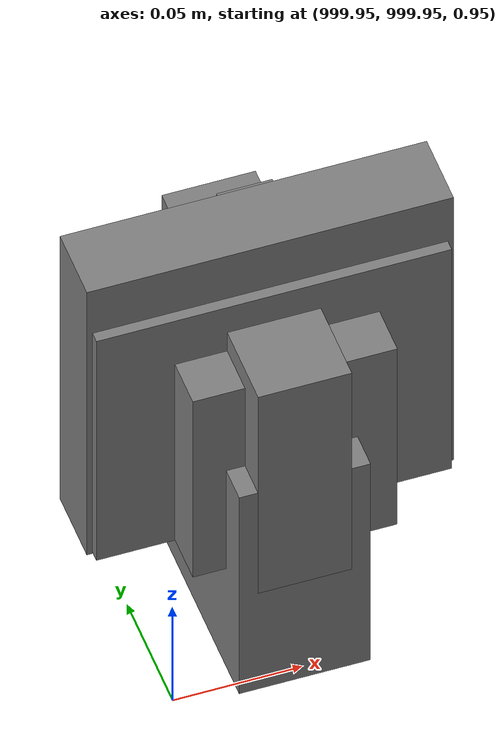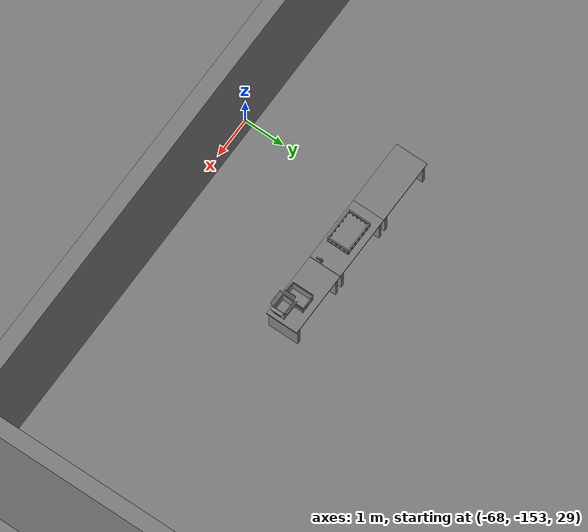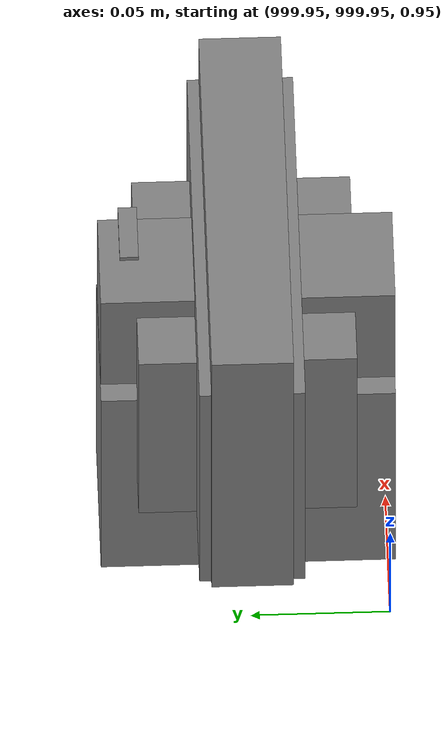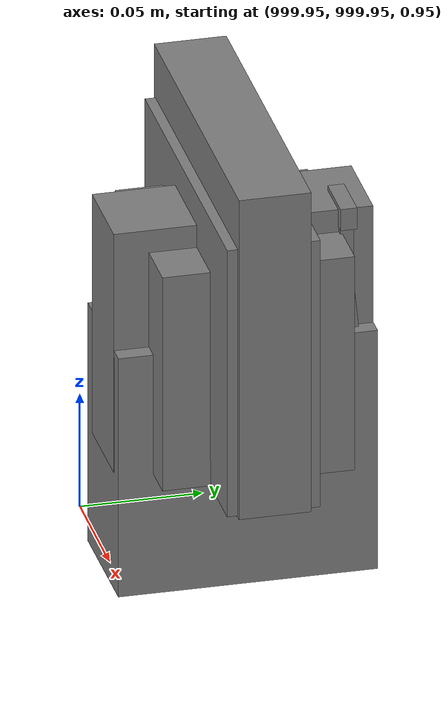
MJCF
<mujoco>
    <option gravity="0.000000000 0.000000000 -9.810000420" timestep="0.0049999999" integrator="implicitfast" density="1.225" viscosity="1.8000001e-05" noslip_iterations="10" iterations="100" sdf_iterations="50">
        <flag multiccd="disable"/>
    </option>
    <size memory="1000M"/>
    <compiler coordinate="local"/>
    <worldbody>
        <light cutoff="30" pos="0 1 1" dir="0 -1 -2"/>
        <light cutoff="30" pos="0 -1 1" dir="0 1 -2"/>
        <body pos="1000.000000000 1000.000000000 1.000000000" euler="0.000000000 0.000000000 180.000000000" name="openloong_gripper_2f85_fix_base_usda_wifi_box">
            <geom contype="1" conaffinity="1" density="1000" type="box" material="" rgba="0.500000000 0.500000000 0.500000000 1.000000000" solimp="0.899999976 0.949999988 0.001000000" friction="1.000000000 0.005000000 0.000100000" solref="0.020000000 1.000000000" margin="0" condim="3" group="0" pos="0.000000000 0.000000000 0.058978677" quat="0.000000000 0.000000047 0.000000000 1.000000000" size="0.068499997 0.018999999 0.059000000" name="openloong_gripper_2f85_fix_base_usda_geom_FBB4A87D_6D66_4657_B307_88C0BF640E6C"/>
            <freejoint name="openloong_gripper_2f85_fix_base_usda_wifi_box_joint"/>
            <site size="0.005000000 0.005000000 0.005000000" rgba="0.500000000 0.500000000 0.500000000 1.000000000" pos="0.000000000 0.000000000 0.000000000" quat="0.999961913 0.008726500 0.000000000 0.000000000" group="0" type="sphere" name="openloong_gripper_2f85_fix_base_usda_wifi_boxsite"/>
        </body>
        <body pos="1000.000000000 1000.000000000 1.000000000" euler="0.000000000 0.000000000 180.000000000" name="openloong_gripper_2f85_fix_base_usda_battery_01">
            <geom contype="1" conaffinity="1" density="1000" type="box" material="" rgba="0.500000000 0.500000000 0.500000000 1.000000000" solimp="0.899999976 0.949999988 0.001000000" friction="1.000000000 0.005000000 0.000100000" solref="0.020000000 1.000000000" margin="0" condim="3" group="0" pos="-0.011123657 -0.041940309 0.101691343" quat="1.000000000 0.000000000 0.000000000 0.000000000" size="0.010800000 0.003375000 0.004725000" name="openloong_gripper_2f85_fix_base_usda_geom_4E8F76B4_3992_43DA_839F_6360C350D5F5"/>
            <geom contype="1" conaffinity="1" density="1000" type="box" material="" rgba="0.500000000 0.500000000 0.500000000 1.000000000" solimp="0.899999976 0.949999988 0.001000000" friction="1.000000000 0.005000000 0.000100000" solref="0.020000000 1.000000000" margin="0" condim="3" group="0" pos="-0.010876465 -0.044247437 0.047066893" quat="0.998702705 -0.050920475 0.000000000 0.000000000" size="0.009450001 0.002700000 0.024975000" name="openloong_gripper_2f85_fix_base_usda_geom_551B6DF6_4F32_4610_884C_CCA166397309"/>
            <geom contype="1" conaffinity="1" density="1000" type="box" material="" rgba="0.500000000 0.500000000 0.500000000 1.000000000" solimp="0.899999976 0.949999988 0.001000000" friction="1.000000000 0.005000000 0.000100000" solref="0.020000000 1.000000000" margin="0" condim="3" group="0" pos="-0.001235962 -0.000659180 0.047381196" quat="1.000000000 0.000000000 0.000000000 0.000000000" size="0.039420001 0.039150000 0.047250003" name="openloong_gripper_2f85_fix_base_usda_geom_3F3EBEA7_E44A_41C8_9D2A_B67BE723A196"/>
            <geom contype="1" conaffinity="1" density="1000" type="box" material="" rgba="0.500000000 0.500000000 0.500000000 1.000000000" solimp="0.899999976 0.949999988 0.001000000" friction="1.000000000 0.005000000 0.000100000" solref="0.020000000 1.000000000" margin="0" condim="3" group="0" pos="-0.010876465 -0.039138794 0.009851727" quat="1.000000000 0.000000000 0.000000000 0.000000000" size="0.009450001 0.010800000 0.013500000" name="openloong_gripper_2f85_fix_base_usda_geom_FB2164D5_BC76_4242_839E_CA46A503BBA2"/>
            <geom contype="1" conaffinity="1" density="1000" type="box" material="" rgba="0.500000000 0.500000000 0.500000000 1.000000000" solimp="0.899999976 0.949999988 0.001000000" friction="1.000000000 0.005000000 0.000100000" solref="0.020000000 1.000000000" margin="0" condim="3" group="0" pos="-0.010876465 -0.041528322 0.071508206" quat="1.000000000 0.000000000 0.000000000 0.000000000" size="0.009450001 0.002700000 0.027000001" name="openloong_gripper_2f85_fix_base_usda_geom_34A11B34_5470_4CCD_894C_F67CF19998E8"/>
            <freejoint name="openloong_gripper_2f85_fix_base_usda_battery_01_joint"/>
            <site size="0.005000000 0.005000000 0.005000000" rgba="0.500000000 0.500000000 0.500000000 1.000000000" pos="0.000000000 0.000000000 0.000000000" quat="0.999961913 0.008726500 0.000000000 0.000000000" group="0" type="sphere" name="openloong_gripper_2f85_fix_base_usda_battery_01site"/>
        </body>
        <body pos="1000.000000000 1000.000000000 1.000000000" euler="0.000000000 0.000000000 180.000000000" name="openloong_gripper_2f85_fix_base_usda_cpu_fan">
            <geom contype="1" conaffinity="1" density="1000" type="box" material="" rgba="0.500000000 0.500000000 0.500000000 1.000000000" solimp="0.899999976 0.949999988 0.001000000" friction="1.000000000 0.005000000 0.000100000" solref="0.020000000 1.000000000" margin="0" condim="3" group="0" pos="0.000000000 0.000000000 0.070034981" quat="0.000000000 0.000000000 0.000000000 1.000000000" size="0.070700005 0.014699999 0.070700005" name="openloong_gripper_2f85_fix_base_usda_geom_6B19A753_5538_40F3_8855_B3F33465E77A"/>
            <freejoint name="openloong_gripper_2f85_fix_base_usda_cpu_fan_joint"/>
            <site size="0.005000000 0.005000000 0.005000000" rgba="0.500000000 0.500000000 0.500000000 1.000000000" pos="0.000000000 0.000000000 0.000000000" quat="0.999961913 0.008726535 0.000000000 0.000000000" group="0" type="sphere" name="openloong_gripper_2f85_fix_base_usda_cpu_fancsite"/>
        </body>
        <body pos="-65.992210388 -149.412643433 31.167079926" euler="-64.508583069 56.753360748 160.712585449" mocap="true" name="spotlight6_SpotLight"/>
        <body pos="1000.000000000 1000.000000000 1.000000000" euler="0.000011953 0.000005123 -179.999984741" name="openloong_gripper_2f85_fix_base_usda_intel_box">
            <geom contype="1" conaffinity="1" density="1000" type="box" material="" rgba="0.500000000 0.500000000 0.500000000 1.000000000" solimp="0.899999976 0.949999988 0.001000000" friction="1.000000000 0.005000000 0.000100000" solref="0.020000000 1.000000000" margin="0" condim="3" group="0" pos="0.000000000 -0.000067139 0.000082284" quat="0.707106709 0.000000225 0.000000253 0.707106650" size="0.052800003 0.025300000 0.052800003" name="openloong_gripper_2f85_fix_base_usda_geom_08DC2F62_05CF_47A9_B98A_D8A40E30735B"/>
            <freejoint name="openloong_gripper_2f85_fix_base_usda_intel_box_joint"/>
            <site size="0.005000000 0.005000000 0.005000000" rgba="0.500000000 0.500000000 0.500000000 1.000000000" pos="0.000000000 0.000000000 0.000000000" quat="0.999961913 0.008726500 0.000000000 0.000000000" group="0" type="sphere" name="openloong_gripper_2f85_fix_base_usda_intel_boxsite"/>
        </body>
        <body pos="1000.000000000 999.999938965 1.000000000" euler="0.000000000 0.000000000 180.000000000" name="openloong_gripper_2f85_fix_base_usda_intelcore_i5">
            <geom contype="1" conaffinity="1" density="1000" type="box" material="" rgba="0.500000000 0.500000000 0.500000000 1.000000000" solimp="0.899999976 0.949999988 0.001000000" friction="1.000000000 0.005000000 0.000100000" solref="0.020000000 1.000000000" margin="0" condim="3" group="0" pos="0.000000000 0.000000000 0.051722717" quat="0.707106709 0.000000000 0.000000000 -0.707106769" size="0.052800000 0.018080002 0.052800000" name="openloong_gripper_2f85_fix_base_usda_geom_DA7B40B9_F634_4D1D_B15E_52F905399076"/>
            <freejoint name="openloong_gripper_2f85_fix_base_usda_intelcore_i5_joint"/>
            <site size="0.005000000 0.005000000 0.005000000" rgba="0.500000000 0.500000000 0.500000000 1.000000000" pos="0.000000000 0.000000000 0.000000000" quat="0.999961913 0.008726534 0.000000000 0.000000000" group="0" type="sphere" name="openloong_gripper_2f85_fix_base_usda_intelcore_i5site"/>
        </body>
        <body pos="-66.267845154 -149.064819336 31.163568497" euler="-56.065685272 -21.981018066 136.645187378" mocap="true" name="spotlight2_SpotLight"/>
        <body pos="-66.185081482 -149.699783325 31.166019440" euler="129.432632446 19.198961258 72.716987610" mocap="true" name="spotlight1_SpotLight"/>
        <body pos="-64.866622925 -149.383972168 30.183746338" euler="89.999984741 89.999946594 0.000000000" name="openloong_gripper_2f85_fix_base_usda_bluebox_01">
            <geom contype="1" conaffinity="1" density="1000" type="box" material="" rgba="0.500000000 0.500000000 0.500000000 1.000000000" solimp="0.899999976 0.949999988 0.001000000" friction="1.000000000 0.005000000 0.000100000" solref="0.020000000 1.000000000" margin="0" condim="3" group="0" pos="0.276580811 0.187225342 0.000068665" quat="0.707106948 0.000077471 0.707106352 0.000077486" size="0.100000001 0.057999998 0.010000000" name="openloong_gripper_2f85_fix_base_usda_geom_694CCD46_FE58_45B6_A39F_2CE7DBEE5E1E"/>
            <geom contype="1" conaffinity="1" density="1000" type="box" material="" rgba="0.500000000 0.500000000 0.500000000 1.000000000" solimp="0.899999976 0.949999988 0.001000000" friction="1.000000000 0.005000000 0.000100000" solref="0.020000000 1.000000000" margin="0" condim="3" group="0" pos="0.000000000 0.002883911 0.000000000" quat="0.999999881 0.000000000 0.000000000 0.000000000" size="0.254000008 0.003000000 0.172000006" name="openloong_gripper_2f85_fix_base_usda_geom_55C6CE2A_EDBE_40F2_9025_A7AF7C576634"/>
            <geom contype="1" conaffinity="1" density="1000" type="box" material="" rgba="0.500000000 0.500000000 0.500000000 1.000000000" solimp="0.899999976 0.949999988 0.001000000" friction="1.000000000 0.005000000 0.000100000" solref="0.020000000 1.000000000" margin="0" condim="3" group="0" pos="0.000000000 0.124874115 0.173484802" quat="0.999796331 0.020176515 -0.000000015 0.000000030" size="0.259999990 0.119999997 0.007000000" name="openloong_gripper_2f85_fix_base_usda_geom_2AAFCFC0_31B9_4AD9_8FFC_7BBE0B183DC8"/>
            <geom contype="1" conaffinity="1" density="1000" type="box" material="" rgba="0.500000000 0.500000000 0.500000000 1.000000000" solimp="0.899999976 0.949999988 0.001000000" friction="1.000000000 0.005000000 0.000100000" solref="0.020000000 1.000000000" margin="0" condim="3" group="0" pos="0.000000000 0.124874115 -0.173469543" quat="0.999796331 -0.020176545 -0.000000015 0.000000000" size="0.259999990 0.119999997 0.007000000" name="openloong_gripper_2f85_fix_base_usda_geom_5291BE75_EF50_40DC_AD39_8D26AA48300E"/>
            <geom contype="1" conaffinity="1" density="1000" type="box" material="" rgba="0.500000000 0.500000000 0.500000000 1.000000000" solimp="0.899999976 0.949999988 0.001000000" friction="1.000000000 0.005000000 0.000100000" solref="0.020000000 1.000000000" margin="0" condim="3" group="0" pos="0.000000000 0.214008331 0.188980103" quat="0.999912977 0.013176724 0.000000015 0.000000000" size="0.259999990 0.029999999 0.012500000" name="openloong_gripper_2f85_fix_base_usda_geom_852D7F34_D17C_4383_84AD_34F9C0D3FD38"/>
            <geom contype="1" conaffinity="1" density="1000" type="box" material="" rgba="0.500000000 0.500000000 0.500000000 1.000000000" solimp="0.899999976 0.949999988 0.001000000" friction="1.000000000 0.005000000 0.000100000" solref="0.020000000 1.000000000" margin="0" condim="3" group="0" pos="-0.258361816 0.125289917 0.001876831" quat="0.702796936 -0.020792112 0.710783124 0.020769298" size="0.189999998 0.119999997 0.009000000" name="openloong_gripper_2f85_fix_base_usda_geom_C23CF25B_AA9F_4B99_9D45_597432493DB0"/>
            <geom contype="1" conaffinity="1" density="1000" type="box" material="" rgba="0.500000000 0.500000000 0.500000000 1.000000000" solimp="0.899999976 0.949999988 0.001000000" friction="1.000000000 0.005000000 0.000100000" solref="0.020000000 1.000000000" margin="0" condim="3" group="0" pos="0.000000000 0.214008331 -0.188980103" quat="0.999912977 -0.013176769 0.000000030 0.000000015" size="0.259999990 0.029999999 0.012500000" name="openloong_gripper_2f85_fix_base_usda_geom_3804993B_BC90_410C_A287_8BAAE7F3D045"/>
            <geom contype="1" conaffinity="1" density="1000" type="box" material="" rgba="0.500000000 0.500000000 0.500000000 1.000000000" solimp="0.899999976 0.949999988 0.001000000" friction="1.000000000 0.005000000 0.000100000" solref="0.020000000 1.000000000" margin="0" condim="3" group="0" pos="-0.276611328 0.187225342 0.000068665" quat="0.707106650 0.000077441 0.707106709 0.000077456" size="0.100000001 0.057999998 0.010000000" name="openloong_gripper_2f85_fix_base_usda_geom_7B5CF518_3F1A_4CA8_A267_A754E62D02C3"/>
            <geom contype="1" conaffinity="1" density="1000" type="box" material="" rgba="0.500000000 0.500000000 0.500000000 1.000000000" solimp="0.899999976 0.949999988 0.001000000" friction="1.000000000 0.005000000 0.000100000" solref="0.020000000 1.000000000" margin="0" condim="3" group="0" pos="0.258331299 0.125289917 0.001876831" quat="0.702851415 0.018856421 0.710823774 -0.019329369" size="0.189999998 0.119999997 0.009000000" name="openloong_gripper_2f85_fix_base_usda_geom_B7A9C11F_2EEB_4B52_9B0B_8F00E36833AE"/>
            <freejoint name="openloong_gripper_2f85_fix_base_usda_bluebox_01_joint"/>
            <site size="0.005000000 0.005000000 0.005000000" rgba="0.500000000 0.500000000 0.500000000 1.000000000" pos="0.000000000 0.000000000 0.000000000" quat="0.999961913 0.008726534 0.000000000 0.000000000" group="0" type="sphere" name="openloong_gripper_2f85_fix_base_usda_bluebox_01site"/>
        </body>
        <body pos="-64.496299744 -149.491867065 30.235729218" euler="0.000000000 0.000000000 89.999946594" name="openloong_gripper_2f85_fix_base_usda_cardboardbox_01">
            <geom contype="1" conaffinity="1" density="1000" type="box" material="" rgba="0.500000000 0.500000000 0.500000000 1.000000000" solimp="0.899999976 0.949999988 0.001000000" friction="1.000000000 0.005000000 0.000100000" solref="0.020000000 1.000000000" margin="0" condim="3" group="0" pos="-0.003166199 -0.004086494 0.005052090" quat="1.000000000 0.000000000 0.000000000 0.000000000" size="0.142499998 0.177500010 0.005000000" name="openloong_gripper_2f85_fix_base_usda_geom_E714203F_D898_4C38_B6AE_0A3DAC0F9773"/>
            <geom contype="1" conaffinity="1" density="1000" type="box" material="" rgba="0.500000000 0.500000000 0.500000000 1.000000000" solimp="0.899999976 0.949999988 0.001000000" friction="1.000000000 0.005000000 0.000100000" solref="0.020000000 1.000000000" margin="0" condim="3" group="0" pos="-0.003166199 0.170316696 0.150570869" quat="1.000000000 0.000000000 0.000000000 0.000000000" size="0.142499998 0.005000000 0.149999991" name="openloong_gripper_2f85_fix_base_usda_geom_92A6C548_501E_4892_B9C6_9ED223B0AF9E"/>
            <geom contype="1" conaffinity="1" density="1000" type="box" material="" rgba="0.500000000 0.500000000 0.500000000 1.000000000" solimp="0.899999976 0.949999988 0.001000000" friction="1.000000000 0.005000000 0.000100000" solref="0.020000000 1.000000000" margin="0" condim="3" group="0" pos="-0.147399902 -0.005307198 0.150570869" quat="1.000000000 0.000000000 0.000000000 0.000000000" size="0.005000000 0.177500010 0.149999991" name="openloong_gripper_2f85_fix_base_usda_geom_CF78481A_A513_448E_8781_B3805DAFCFAE"/>
            <geom contype="1" conaffinity="1" density="1000" type="box" material="" rgba="0.500000000 0.500000000 0.500000000 1.000000000" solimp="0.899999976 0.949999988 0.001000000" friction="1.000000000 0.005000000 0.000100000" solref="0.020000000 1.000000000" margin="0" condim="3" group="0" pos="0.140275955 -0.005307198 0.150570869" quat="1.000000000 0.000000000 0.000000000 0.000000000" size="0.005000000 0.177500010 0.149999991" name="openloong_gripper_2f85_fix_base_usda_geom_C986BF74_DE46_4A56_BD07_EC9D7EE8A6B3"/>
            <geom contype="1" conaffinity="1" density="1000" type="box" material="" rgba="0.500000000 0.500000000 0.500000000 1.000000000" solimp="0.899999976 0.949999988 0.001000000" friction="1.000000000 0.005000000 0.000100000" solref="0.020000000 1.000000000" margin="0" condim="3" group="0" pos="-0.003166199 -0.181550980 0.150570869" quat="1.000000000 0.000000000 0.000000000 0.000000000" size="0.142499998 0.005000000 0.149999991" name="openloong_gripper_2f85_fix_base_usda_geom_454CCEA9_C7FD_48D7_9722_044BA6A65987"/>
            <freejoint name="openloong_gripper_2f85_fix_base_usda_cardboardbox_01_joint"/>
            <site size="0.005000000 0.005000000 0.005000000" rgba="0.500000000 0.500000000 0.500000000 1.000000000" pos="0.000000000 0.000000000 0.000000000" quat="0.999961913 0.008726535 0.000000000 0.000000000" group="0" type="sphere" name="openloong_gripper_2f85_fix_base_usda_site_394C0EDE_37C4_439F_A5DD_CEBE15A70720"/>
            <body pos="0.139160156 -0.004048347 0.301930904" euler="-179.999954224 49.383502960 179.999954224" name="openloong_gripper_2f85_fix_base_usda_A1_006">
                <geom contype="1" conaffinity="1" density="1000" type="box" material="" rgba="0.500000000 0.500000000 0.500000000 1.000000000" solimp="0.899999976 0.949999988 0.001000000" friction="1.000000000 0.005000000 0.000100000" solref="0.020000000 1.000000000" margin="0" condim="3" group="0" pos="-0.071587563 0.000009537 0.001745224" quat="0.999999881 0.000000000 0.000000000 0.000000000" size="0.071249999 0.179999992 0.002500000" name="openloong_gripper_2f85_fix_base_usda_geom_FD0288FA_991B_461F_BC00_AAC793C2D8D5"/>
                <joint armature="0" stiffness="0.07" damping="0.0099999998" axis="0.000000 1.000000 0.000000" type="hinge" name="openloong_gripper_2f85_fix_base_usda_A1_006"/>
            </body>
            <body pos="-0.145902634 -0.004086494 0.301938057" euler="-180.000000000 -60.000011444 -180.000000000" name="openloong_gripper_2f85_fix_base_usda_A2_006">
                <geom contype="1" conaffinity="1" density="1000" type="box" material="" rgba="0.500000000 0.500000000 0.500000000 1.000000000" solimp="0.899999976 0.949999988 0.001000000" friction="1.000000000 0.005000000 0.000100000" solref="0.020000000 1.000000000" margin="0" condim="3" group="0" pos="0.071268082 0.000009537 0.002717972" quat="0.000002921 0.000000000 -0.000000030 0.999999881" size="0.071249999 0.179999992 0.002500000" name="openloong_gripper_2f85_fix_base_usda_geom_EBD9768E_4584_4DF2_91E6_F40D5381DB87"/>
                <joint armature="0" stiffness="0.07" damping="0.0099999998" axis="0.000000 1.000000 0.000000" type="hinge" name="openloong_gripper_2f85_fix_base_usda_A2_006"/>
            </body>
            <body pos="-0.003385544 0.175991058 0.301930904" euler="-125.858116150 -0.000004561 0.000002331" name="openloong_gripper_2f85_fix_base_usda_B2_006">
                <geom contype="1" conaffinity="1" density="1000" type="box" material="" rgba="0.500000000 0.500000000 0.500000000 1.000000000" solimp="0.899999976 0.949999988 0.001000000" friction="1.000000000 0.005000000 0.000100000" solref="0.020000000 1.000000000" margin="0" condim="3" group="0" pos="0.000009537 -0.070939064 -0.002470016" quat="0.999614120 0.027776197 -0.000000015 0.000000030" size="0.137500003 0.064999998 0.005000000" name="openloong_gripper_2f85_fix_base_usda_geom_E63DA7F0_0064_4F98_B3FE_B69AA08EE3D6"/>
                <joint armature="0" stiffness="0.07" damping="0.0099999998" axis="1.000000 0.000000 0.000000" type="hinge" name="openloong_gripper_2f85_fix_base_usda_B2_006"/>
            </body>
            <body pos="-0.003385544 -0.184140205 0.301938057" euler="147.805557251 0.000000000 0.000000000" name="openloong_gripper_2f85_fix_base_usda_B1_006">
                <geom contype="1" conaffinity="1" density="1000" type="box" material="" rgba="0.500000000 0.500000000 0.500000000 1.000000000" solimp="0.899999976 0.949999988 0.001000000" friction="1.000000000 0.005000000 0.000100000" solref="0.020000000 1.000000000" margin="0" condim="3" group="0" pos="-0.000028610 0.070202351 -0.002703667" quat="0.999614179 -0.027776167 0.000000000 0.000000000" size="0.137500003 0.064999998 0.005000000" name="openloong_gripper_2f85_fix_base_usda_geom_D745034C_EEC3_43C8_A680_60E6B2E78377"/>
                <joint armature="0" stiffness="0.07" damping="0.0099999998" axis="1.000000 0.000000 0.000000" type="hinge" name="openloong_gripper_2f85_fix_base_usda_B1_006"/>
            </body>
        </body>
        <body pos="-65.882858276 -149.481979370 30.229999542" euler="-64.487716675 0.000000000 0.000000000" name="openloong_gripper_2f85_fix_base_usda_Barcode">
            <geom contype="1" conaffinity="1" density="1000" type="box" material="" rgba="0.500000000 0.500000000 0.500000000 1.000000000" solimp="0.899999976 0.949999988 0.001000000" friction="1.000000000 0.005000000 0.000100000" solref="0.020000000 1.000000000" margin="0" condim="3" group="0" pos="0.000000000 0.013038635 0.001419067" quat="0.000000000 0.000000000 0.000000000 1.000000119" size="0.034000002 0.010000000 0.017999999" name="openloong_gripper_2f85_fix_base_usda_geom_E67D697D_96ED_46B0_BFFB_A2D93F3541FB"/>
            <geom contype="1" conaffinity="1" density="1000" type="box" material="" rgba="0.500000000 0.500000000 0.500000000 1.000000000" solimp="0.899999976 0.949999988 0.001000000" friction="1.000000000 0.005000000 0.000100000" solref="0.020000000 1.000000000" margin="0" condim="3" group="0" pos="0.000000000 -0.035301208 -0.007095337" quat="0.000000000 0.000000000 -0.043619365 0.999048233" size="0.028999999 0.010000000 0.020000000" name="openloong_gripper_2f85_fix_base_usda_geom_EF4B34CD_AD64_476F_B8B2_DF177033B56F"/>
            <geom contype="1" conaffinity="1" density="1000" type="box" material="" rgba="0.500000000 0.500000000 0.500000000 1.000000000" solimp="0.899999976 0.949999988 0.001000000" friction="1.000000000 0.005000000 0.000100000" solref="0.020000000 1.000000000" margin="0" condim="3" group="0" pos="0.000000000 -0.043411255 -0.011749268" quat="0.922262907 0.386563420 0.000000000 0.000000000" size="0.026000001 0.010000000 0.020000000" name="openloong_gripper_2f85_fix_base_usda_geom_C4B27C39_590E_47D8_B982_8A6F97E98D05"/>
            <geom contype="1" conaffinity="1" density="1000" type="box" material="" rgba="0.500000000 0.500000000 0.500000000 1.000000000" solimp="0.899999976 0.949999988 0.001000000" friction="1.000000000 0.005000000 0.000100000" solref="0.020000000 1.000000000" margin="0" condim="3" group="0" pos="0.000000000 -0.016967773 -0.031860352" quat="0.000000000 0.000000000 0.000000000 1.000000119" size="0.008000000 0.010000000 0.013000000" name="openloong_gripper_2f85_fix_base_usda_geom_D8CB5BEE_3E79_4552_BF75_22ECE30A1B4E"/>
            <geom contype="1" conaffinity="1" density="1000" type="box" material="" rgba="0.500000000 0.500000000 0.500000000 1.000000000" solimp="0.899999976 0.949999988 0.001000000" friction="1.000000000 0.005000000 0.000100000" solref="0.020000000 1.000000000" margin="0" condim="3" group="0" pos="0.000000000 -0.001869202 0.000312805" quat="0.953716993 0.300705761 0.000000000 0.000000000" size="0.032000002 0.010000000 0.018999999" name="openloong_gripper_2f85_fix_base_usda_geom_727A6116_1F39_42C8_A050_7C9124A042C0"/>
            <geom contype="1" conaffinity="1" density="1000" type="box" material="" rgba="0.500000000 0.500000000 0.500000000 1.000000000" solimp="0.899999976 0.949999988 0.001000000" friction="1.000000000 0.005000000 0.000100000" solref="0.020000000 1.000000000" margin="0" condim="3" group="0" pos="0.000000000 -0.019531250 -0.003173828" quat="0.953716993 0.300705761 0.000000000 0.000000000" size="0.030999999 0.010000000 0.020000000" name="openloong_gripper_2f85_fix_base_usda_geom_3489380C_C1F5_408A_B9AD_5CE12FBA7D5D"/>
            <geom contype="1" conaffinity="1" density="1000" type="box" material="" rgba="0.500000000 0.500000000 0.500000000 1.000000000" solimp="0.899999976 0.949999988 0.001000000" friction="1.000000000 0.005000000 0.000100000" solref="0.020000000 1.000000000" margin="0" condim="3" group="0" pos="0.000000000 -0.035301208 -0.007095337" quat="0.953716993 0.300705761 0.000000000 0.000000000" size="0.028999999 0.010000000 0.020000000" name="openloong_gripper_2f85_fix_base_usda_geom_8192BF1A_F810_4569_8076_717A41F70C89"/>
            <geom contype="1" conaffinity="1" density="1000" type="box" material="" rgba="0.500000000 0.500000000 0.500000000 1.000000000" solimp="0.899999976 0.949999988 0.001000000" friction="1.000000000 0.005000000 0.000100000" solref="0.020000000 1.000000000" margin="0" condim="3" group="0" pos="0.000000000 -0.042617798 -0.071121216" quat="0.000000000 0.000000000 0.000000000 1.000000119" size="0.013000000 0.021000000 0.059999999" name="openloong_gripper_2f85_fix_base_usda_geom_0B96286D_4807_43F1_A6E6_AD204390F96B"/>
            <freejoint name="openloong_gripper_2f85_fix_base_usda_Barcode_joint"/>
            <site size="0.005000000 0.005000000 0.005000000" rgba="0.500000000 0.500000000 0.500000000 1.000000000" pos="0.000000000 0.000000000 0.000000000" quat="1.000000000 0.000000000 0.000000000 0.000000000" group="0" type="sphere" name="openloong_gripper_2f85_fix_base_usda_Barcode_site"/>
        </body>
        <body pos="-66.745018005 -149.392349243 30.184000015" euler="0.000000000 0.000000000 89.999946594" name="[22330831892600]_Basket_01">
            <geom contype="1" conaffinity="1" density="1000" type="box" material="" rgba="0.500000000 0.500000000 0.500000000 1.000000000" solimp="0.899999976 0.949999988 0.001000000" friction="1.000000000 0.005000000 0.000100000" solref="0.020000000 1.000000000" margin="0" condim="3" group="0" pos="-0.052425385 0.389207840 0.089787483" quat="0.707107008 0.000000000 0.000000000 0.707106411" size="0.014249999 0.014249999 0.059999999" name="[22330831892600]_geom_EFCD44BE_59E6_42F1_8522_6987A8E51151"/>
            <geom contype="1" conaffinity="1" density="1000" type="box" material="" rgba="0.500000000 0.500000000 0.500000000 1.000000000" solimp="0.899999976 0.949999988 0.001000000" friction="1.000000000 0.005000000 0.000100000" solref="0.020000000 1.000000000" margin="0" condim="3" group="0" pos="0.264015198 -0.133043289 0.089787483" quat="0.707107008 0.000000000 0.000000000 0.707106411" size="0.014249999 0.014249999 0.059999999" name="[22330831892600]_geom_120C0FA5_72B9_4C8E_8056_0D32730AC964"/>
            <geom contype="1" conaffinity="1" density="1000" type="box" material="" rgba="0.500000000 0.500000000 0.500000000 1.000000000" solimp="0.899999976 0.949999988 0.001000000" friction="1.000000000 0.005000000 0.000100000" solref="0.020000000 1.000000000" margin="0" condim="3" group="0" pos="-0.264015198 -0.265548706 0.089793205" quat="0.707107008 0.000000000 0.000000000 0.707106411" size="0.014249999 0.014249999 0.059999999" name="[22330831892600]_geom_4DEB3CC5_F51C_4A55_B746_6E541E7F821F"/>
            <geom contype="1" conaffinity="1" density="1000" type="box" material="" rgba="0.500000000 0.500000000 0.500000000 1.000000000" solimp="0.899999976 0.949999988 0.001000000" friction="1.000000000 0.005000000 0.000100000" solref="0.020000000 1.000000000" margin="0" condim="3" group="0" pos="-0.160263062 -0.389322281 0.089793205" quat="0.707107008 0.000000000 0.000000000 0.707106411" size="0.014249999 0.014249999 0.059999999" name="[22330831892600]_geom_21416080_2C04_4978_BA5A_E69FE956BF75"/>
            <geom contype="1" conaffinity="1" density="1000" type="box" material="" rgba="0.500000000 0.500000000 0.500000000 1.000000000" solimp="0.899999976 0.949999988 0.001000000" friction="1.000000000 0.005000000 0.000100000" solref="0.020000000 1.000000000" margin="0" condim="3" group="0" pos="0.162265778 -0.389322281 0.089787483" quat="0.707107008 0.000000000 0.000000000 0.707106411" size="0.014249999 0.014249999 0.059999999" name="[22330831892600]_geom_AF1D475F_F97E_4FCB_B9EA_B5ACA0543DEB"/>
            <geom contype="1" conaffinity="1" density="1000" type="box" material="" rgba="0.500000000 0.500000000 0.500000000 1.000000000" solimp="0.899999976 0.949999988 0.001000000" friction="1.000000000 0.005000000 0.000100000" solref="0.020000000 1.000000000" margin="0" condim="3" group="0" pos="0.264015198 0.389207840 0.089787483" quat="0.707107008 0.000000000 0.000000000 0.707106411" size="0.014249999 0.014249999 0.059999999" name="[22330831892600]_geom_C5C8BEE0_2E6A_41A6_BABA_1F197E49C5E7"/>
            <geom contype="1" conaffinity="1" density="1000" type="box" material="" rgba="0.500000000 0.500000000 0.500000000 1.000000000" solimp="0.899999976 0.949999988 0.001000000" friction="1.000000000 0.005000000 0.000100000" solref="0.020000000 1.000000000" margin="0" condim="3" group="0" pos="-0.264015198 -0.133043289 0.089793205" quat="0.707107008 0.000000000 0.000000000 0.707106411" size="0.014249999 0.014249999 0.059999999" name="[22330831892600]_geom_E058D4E4_51D6_43DF_A456_105F761CCF55"/>
            <geom contype="1" conaffinity="1" density="1000" type="box" material="" rgba="0.500000000 0.500000000 0.500000000 1.000000000" solimp="0.899999976 0.949999988 0.001000000" friction="1.000000000 0.005000000 0.000100000" solref="0.020000000 1.000000000" margin="0" condim="3" group="0" pos="-0.264026642 0.269256592 0.089793205" quat="0.707107008 0.000000000 0.000000000 0.707106411" size="0.014249999 0.014249999 0.059999999" name="[22330831892600]_geom_5E2BC109_C1C4_4BF5_91C4_4FB76F760BE7"/>
            <geom contype="1" conaffinity="1" density="1000" type="box" material="" rgba="0.500000000 0.500000000 0.500000000 1.000000000" solimp="0.899999976 0.949999988 0.001000000" friction="1.000000000 0.005000000 0.000100000" solref="0.020000000 1.000000000" margin="0" condim="3" group="0" pos="0.054462433 0.389207840 0.089787483" quat="0.707107008 0.000000000 0.000000000 0.707106411" size="0.014249999 0.014249999 0.059999999" name="[22330831892600]_geom_889B883F_D886_4E73_8260_922C069B4EC7"/>
            <geom contype="1" conaffinity="1" density="1000" type="box" material="" rgba="0.500000000 0.500000000 0.500000000 1.000000000" solimp="0.899999976 0.949999988 0.001000000" friction="1.000000000 0.005000000 0.000100000" solref="0.020000000 1.000000000" margin="0" condim="3" group="0" pos="0.054462433 -0.389322281 0.089787483" quat="0.707107008 0.000000000 0.000000000 0.707106411" size="0.014249999 0.014249999 0.059999999" name="[22330831892600]_geom_956985FD_DC66_4EBD_A24F_BFDC51DE8D21"/>
            <geom contype="1" conaffinity="1" density="1000" type="box" material="" rgba="0.500000000 0.500000000 0.500000000 1.000000000" solimp="0.899999976 0.949999988 0.001000000" friction="1.000000000 0.005000000 0.000100000" solref="0.020000000 1.000000000" margin="0" condim="3" group="0" pos="0.264015198 0.269256592 0.089793205" quat="0.707107008 0.000000000 0.000000000 0.707106411" size="0.014249999 0.014249999 0.059999999" name="[22330831892600]_geom_63FCC4CF_DEBD_4F7E_B1DB_2A9C1D8A8FCD"/>
            <geom contype="1" conaffinity="1" density="1000" type="box" material="" rgba="0.500000000 0.500000000 0.500000000 1.000000000" solimp="0.899999976 0.949999988 0.001000000" friction="1.000000000 0.005000000 0.000100000" solref="0.020000000 1.000000000" margin="0" condim="3" group="0" pos="0.264015198 -0.389322281 0.089787483" quat="0.707107008 0.000000000 0.000000000 0.707106411" size="0.014249999 0.014249999 0.059999999" name="[22330831892600]_geom_E6B46EDD_6EB7_49F1_841B_5CD11AD6E2A6"/>
            <geom contype="1" conaffinity="1" density="1000" type="box" material="" rgba="0.500000000 0.500000000 0.500000000 1.000000000" solimp="0.899999976 0.949999988 0.001000000" friction="1.000000000 0.005000000 0.000100000" solref="0.020000000 1.000000000" margin="0" condim="3" group="0" pos="0.000000000 0.000000000 0.015998840" quat="0.707107008 0.000000000 0.000000000 0.707106411" size="0.403499991 0.279000014 0.015750000" name="[22330831892600]_geom_BE95086C_B60B_4842_9FA2_77C91BB97507"/>
            <geom contype="1" conaffinity="1" density="1000" type="box" material="" rgba="0.500000000 0.500000000 0.500000000 1.000000000" solimp="0.899999976 0.949999988 0.001000000" friction="1.000000000 0.005000000 0.000100000" solref="0.020000000 1.000000000" margin="0" condim="3" group="0" pos="0.000000000 -0.389476776 0.163619041" quat="0.707107008 0.000000000 0.000000000 0.707106411" size="0.015000000 0.277500004 0.015750000" name="[22330831892600]_geom_403D30DB_5D79_4AFD_8198_B2AFFC225FEF"/>
            <geom contype="1" conaffinity="1" density="1000" type="box" material="" rgba="0.500000000 0.500000000 0.500000000 1.000000000" solimp="0.899999976 0.949999988 0.001000000" friction="1.000000000 0.005000000 0.000100000" solref="0.020000000 1.000000000" margin="0" condim="3" group="0" pos="0.162265778 0.389207840 0.089787483" quat="0.707107008 0.000000000 0.000000000 0.707106411" size="0.014249999 0.014249999 0.059999999" name="[22330831892600]_geom_28E29FB2_AE1A_4307_BF93_575E09ABBE5B"/>
            <geom contype="1" conaffinity="1" density="1000" type="box" material="" rgba="0.500000000 0.500000000 0.500000000 1.000000000" solimp="0.899999976 0.949999988 0.001000000" friction="1.000000000 0.005000000 0.000100000" solref="0.020000000 1.000000000" margin="0" condim="3" group="0" pos="0.000000000 0.389471054 0.163619041" quat="0.707107008 0.000000000 0.000000000 0.707106411" size="0.015000000 0.277500004 0.015750000" name="[22330831892600]_geom_CDA65CA2_0901_4528_AA88_629293F50DB8"/>
            <geom contype="1" conaffinity="1" density="1000" type="box" material="" rgba="0.500000000 0.500000000 0.500000000 1.000000000" solimp="0.899999976 0.949999988 0.001000000" friction="1.000000000 0.005000000 0.000100000" solref="0.020000000 1.000000000" margin="0" condim="3" group="0" pos="-0.263511658 0.000000000 0.163619041" quat="0.707107008 0.000000000 0.000000000 0.707106411" size="0.403499991 0.015000000 0.015750000" name="[22330831892600]_geom_EAF033E9_4933_47E5_8317_D9AF76DE084E"/>
            <geom contype="1" conaffinity="1" density="1000" type="box" material="" rgba="0.500000000 0.500000000 0.500000000 1.000000000" solimp="0.899999976 0.949999988 0.001000000" friction="1.000000000 0.005000000 0.000100000" solref="0.020000000 1.000000000" margin="0" condim="3" group="0" pos="-0.264015198 0.141334534 0.089793205" quat="0.707107008 0.000000000 0.000000000 0.707106411" size="0.014249999 0.014249999 0.059999999" name="[22330831892600]_geom_39BFDABE_EB77_4540_9576_72CCFE2D8DEB"/>
            <geom contype="1" conaffinity="1" density="1000" type="box" material="" rgba="0.500000000 0.500000000 0.500000000 1.000000000" solimp="0.899999976 0.949999988 0.001000000" friction="1.000000000 0.005000000 0.000100000" solref="0.020000000 1.000000000" margin="0" condim="3" group="0" pos="0.264015198 -0.265548706 0.089787483" quat="0.707107008 0.000000000 0.000000000 0.707106411" size="0.014249999 0.014249999 0.059999999" name="[22330831892600]_geom_6FF3B286_CF58_4813_AE2C_C7344D830AD2"/>
            <geom contype="1" conaffinity="1" density="1000" type="box" material="" rgba="0.500000000 0.500000000 0.500000000 1.000000000" solimp="0.899999976 0.949999988 0.001000000" friction="1.000000000 0.005000000 0.000100000" solref="0.020000000 1.000000000" margin="0" condim="3" group="0" pos="-0.160263062 0.389207840 0.089787483" quat="0.707107008 0.000000000 0.000000000 0.707106411" size="0.014249999 0.014249999 0.059999999" name="[22330831892600]_geom_2A90A892_6F33_445D_B019_50016F7B14D0"/>
            <geom contype="1" conaffinity="1" density="1000" type="box" material="" rgba="0.500000000 0.500000000 0.500000000 1.000000000" solimp="0.899999976 0.949999988 0.001000000" friction="1.000000000 0.005000000 0.000100000" solref="0.020000000 1.000000000" margin="0" condim="3" group="0" pos="-0.052425385 -0.389322281 0.089787483" quat="0.707107008 0.000000000 0.000000000 0.707106411" size="0.014249999 0.014249999 0.059999999" name="[22330831892600]_geom_C08BF101_FBF3_4420_8FE8_2D24EBFCE850"/>
            <geom contype="1" conaffinity="1" density="1000" type="box" material="" rgba="0.500000000 0.500000000 0.500000000 1.000000000" solimp="0.899999976 0.949999988 0.001000000" friction="1.000000000 0.005000000 0.000100000" solref="0.020000000 1.000000000" margin="0" condim="3" group="0" pos="-0.264026642 -0.389322281 0.089793205" quat="0.707107008 0.000000000 0.000000000 0.707106411" size="0.014249999 0.014249999 0.059999999" name="[22330831892600]_geom_9B678811_F131_4531_8163_A5F4C09B5311"/>
            <geom contype="1" conaffinity="1" density="1000" type="box" material="" rgba="0.500000000 0.500000000 0.500000000 1.000000000" solimp="0.899999976 0.949999988 0.001000000" friction="1.000000000 0.005000000 0.000100000" solref="0.020000000 1.000000000" margin="0" condim="3" group="0" pos="0.264015198 0.141334534 0.089787483" quat="0.707107008 0.000000000 0.000000000 0.707106411" size="0.014249999 0.014249999 0.059999999" name="[22330831892600]_geom_B53C6FB5_A004_45EA_84FD_9E4E3532F51E"/>
            <geom contype="1" conaffinity="1" density="1000" type="box" material="" rgba="0.500000000 0.500000000 0.500000000 1.000000000" solimp="0.899999976 0.949999988 0.001000000" friction="1.000000000 0.005000000 0.000100000" solref="0.020000000 1.000000000" margin="0" condim="3" group="0" pos="-0.264015198 0.389207840 0.089793205" quat="0.707107008 0.000000000 0.000000000 0.707106411" size="0.014249999 0.014249999 0.059999999" name="[22330831892600]_geom_7F8702A3_93B6_4FDB_9D77_D7C83FAAFDF9"/>
            <geom contype="1" conaffinity="1" density="1000" type="box" material="" rgba="0.500000000 0.500000000 0.500000000 1.000000000" solimp="0.899999976 0.949999988 0.001000000" friction="1.000000000 0.005000000 0.000100000" solref="0.020000000 1.000000000" margin="0" condim="3" group="0" pos="0.264015198 0.004480362 0.089787483" quat="0.707107008 0.000000000 0.000000000 0.707106411" size="0.014249999 0.014249999 0.059999999" name="[22330831892600]_geom_BDF6C234_4712_4DB3_995D_CF54B0E2679C"/>
            <geom contype="1" conaffinity="1" density="1000" type="box" material="" rgba="0.500000000 0.500000000 0.500000000 1.000000000" solimp="0.899999976 0.949999988 0.001000000" friction="1.000000000 0.005000000 0.000100000" solref="0.020000000 1.000000000" margin="0" condim="3" group="0" pos="0.263694763 -0.000011444 0.163619041" quat="0.707107008 0.000000000 0.000000000 0.707106411" size="0.403499991 0.015000000 0.015750000" name="[22330831892600]_geom_BCE57E51_03BF_4C98_B99C_05A43DBD69FD"/>
            <geom contype="1" conaffinity="1" density="1000" type="box" material="" rgba="0.500000000 0.500000000 0.500000000 1.000000000" solimp="0.899999976 0.949999988 0.001000000" friction="1.000000000 0.005000000 0.000100000" solref="0.020000000 1.000000000" margin="0" condim="3" group="0" pos="-0.264015198 0.004480362 0.089793205" quat="0.707107008 0.000000000 0.000000000 0.707106411" size="0.014249999 0.014249999 0.059999999" name="[22330831892600]_geom_E0325BAA_E914_40ED_8B01_3E2E2F53B32E"/>
            <freejoint name="[22330831892600]_joint_0B5451B6_B740_421F_8F0D_A8A0029BF683"/>
        </body>
        <body pos="0.000000000 0.000000000 0.000000000" euler="0.000000000 0.000000000 0.000000000" name="Static Objects_Static Objects">
            <geom contype="1" conaffinity="1" density="1000" type="box" material="" rgba="0.500000000 0.500000000 0.500000000 1.000000000" solimp="0.899999976 0.949999988 0.001000000" friction="1.000000000 0.005000000 0.000100000" solref="0.020000000 1.000000000" margin="0" condim="3" group="0" pos="-67.544113159 -149.365814209 29.727830887" quat="0.500000417 0.499999970 0.499999553 0.499999970" size="0.381000012 0.319999993 0.041000001" name="Static Objects_geom_5C425FB2_8691_4454_8B8E_80C4350DA798"/>
            <geom contype="1" conaffinity="1" density="1000" type="box" material="" rgba="0.500000000 0.500000000 0.500000000 1.000000000" solimp="0.899999976 0.949999988 0.001000000" friction="1.000000000 0.005000000 0.000100000" solref="0.020000000 1.000000000" margin="0" condim="3" group="0" pos="-68.239501953 -149.365814209 30.086868286" quat="0.500000417 0.499999970 0.499999553 0.499999970" size="0.370999992 0.039500002 0.745000005" name="Static Objects_geom_A2825147_0909_4F2F_8DCA_14AD40720855"/>
            <geom contype="1" conaffinity="1" density="1000" type="box" material="" rgba="0.500000000 0.500000000 0.500000000 1.000000000" solimp="0.899999976 0.949999988 0.001000000" friction="1.000000000 0.005000000 0.000100000" solref="0.020000000 1.000000000" margin="0" condim="3" group="0" pos="-68.239501953 -149.365814209 30.147235870" quat="0.500000417 0.499999970 0.499999553 0.499999970" size="0.400000006 0.022000000 0.800000012" name="Static Objects_geom_72FF025B_D511_4374_9FB8_8950A86B5231"/>
            <geom contype="1" conaffinity="1" density="1000" type="box" material="" rgba="0.500000000 0.500000000 0.500000000 1.000000000" solimp="0.899999976 0.949999988 0.001000000" friction="1.000000000 0.005000000 0.000100000" solref="0.020000000 1.000000000" margin="0" condim="3" group="0" pos="-68.934890747 -149.365814209 29.727830887" quat="0.500000417 0.499999970 0.499999553 0.499999970" size="0.381000012 0.319999993 0.041000001" name="Static Objects_geom_D9A5189C_884B_4E79_848A_9B1E1BF97AE0"/>
            <geom contype="1" conaffinity="1" density="1000" type="box" material="" rgba="0.500000000 0.500000000 0.500000000 1.000000000" solimp="0.899999976 0.949999988 0.001000000" friction="1.000000000 0.005000000 0.000100000" solref="0.020000000 1.000000000" margin="0" condim="3" group="0" pos="-68.239501953 -149.365814209 29.561563492" quat="0.500000417 0.499999970 0.499999553 0.499999970" size="0.020000000 0.022000000 0.660000026" name="Static Objects_geom_DFAF3EEE_1618_4D9F_8711_9D827342F8C8"/>
            <geom contype="1" conaffinity="1" density="1000" type="box" material="" rgba="0.500000000 0.500000000 0.500000000 1.000000000" solimp="0.899999976 0.949999988 0.001000000" friction="1.000000000 0.005000000 0.000100000" solref="0.020000000 1.000000000" margin="0" condim="3" group="0" pos="-65.945671082 -149.365814209 29.727830887" quat="0.500000417 0.499999970 0.499999553 0.499999970" size="0.381000012 0.319999993 0.041000001" name="Static Objects_geom_39AEAC28_A752_421C_BF76_7DB251CBE485"/>
            <geom contype="1" conaffinity="1" density="1000" type="box" material="" rgba="0.500000000 0.500000000 0.500000000 1.000000000" solimp="0.899999976 0.949999988 0.001000000" friction="1.000000000 0.005000000 0.000100000" solref="0.020000000 1.000000000" margin="0" condim="3" group="0" pos="-66.641059875 -149.365814209 30.086868286" quat="0.500000417 0.499999970 0.499999553 0.499999970" size="0.370999992 0.039500002 0.745000005" name="Static Objects_geom_4A0F457F_CF58_4ECF_94A1_16384BBD465A"/>
            <geom contype="1" conaffinity="1" density="1000" type="box" material="" rgba="0.500000000 0.500000000 0.500000000 1.000000000" solimp="0.899999976 0.949999988 0.001000000" friction="1.000000000 0.005000000 0.000100000" solref="0.020000000 1.000000000" margin="0" condim="3" group="0" pos="-66.641059875 -149.365814209 30.147235870" quat="0.500000417 0.499999970 0.499999553 0.499999970" size="0.400000006 0.022000000 0.800000012" name="Static Objects_geom_C82FB2E1_2D03_4552_9A01_618E4220095C"/>
            <geom contype="1" conaffinity="1" density="1000" type="box" material="" rgba="0.500000000 0.500000000 0.500000000 1.000000000" solimp="0.899999976 0.949999988 0.001000000" friction="1.000000000 0.005000000 0.000100000" solref="0.020000000 1.000000000" margin="0" condim="3" group="0" pos="-67.336448669 -149.365814209 29.727830887" quat="0.500000417 0.499999970 0.499999553 0.499999970" size="0.381000012 0.319999993 0.041000001" name="Static Objects_geom_7D1D9E76_ED9D_4B0C_8D4E_4F4961D9789E"/>
            <geom contype="1" conaffinity="1" density="1000" type="box" material="" rgba="0.500000000 0.500000000 0.500000000 1.000000000" solimp="0.899999976 0.949999988 0.001000000" friction="1.000000000 0.005000000 0.000100000" solref="0.020000000 1.000000000" margin="0" condim="3" group="0" pos="-66.641059875 -149.365814209 29.561563492" quat="0.500000417 0.499999970 0.499999553 0.499999970" size="0.020000000 0.022000000 0.660000026" name="Static Objects_geom_0DDACF27_6F6C_4072_8401_5B35587F80E6"/>
            <geom contype="1" conaffinity="1" density="1000" type="box" material="" rgba="0.500000000 0.500000000 0.500000000 1.000000000" solimp="0.899999976 0.949999988 0.001000000" friction="1.000000000 0.005000000 0.000100000" solref="0.020000000 1.000000000" margin="0" condim="3" group="0" pos="-64.338577271 -149.365814209 29.727830887" quat="0.500000417 0.499999970 0.499999553 0.499999970" size="0.381000012 0.319999993 0.041000001" name="Static Objects_geom_2612B931_1C9F_47E2_AEDE_A7F562B3967C"/>
            <geom contype="1" conaffinity="1" density="1000" type="box" material="" rgba="0.500000000 0.500000000 0.500000000 1.000000000" solimp="0.899999976 0.949999988 0.001000000" friction="1.000000000 0.005000000 0.000100000" solref="0.020000000 1.000000000" margin="0" condim="3" group="0" pos="-65.033966064 -149.365814209 30.086868286" quat="0.500000417 0.499999970 0.499999553 0.499999970" size="0.370999992 0.039500002 0.745000005" name="Static Objects_geom_7FCBFD0B_1F93_4C74_80D1_B64C947D8C1C"/>
            <geom contype="1" conaffinity="1" density="1000" type="box" material="" rgba="0.500000000 0.500000000 0.500000000 1.000000000" solimp="0.899999976 0.949999988 0.001000000" friction="1.000000000 0.005000000 0.000100000" solref="0.020000000 1.000000000" margin="0" condim="3" group="0" pos="-65.033966064 -149.365814209 30.147235870" quat="0.500000417 0.499999970 0.499999553 0.499999970" size="0.400000006 0.022000000 0.800000012" name="Static Objects_geom_D7FD1706_AADC_4558_972D_B68ECD06182C"/>
            <geom contype="1" conaffinity="1" density="1000" type="box" material="" rgba="0.500000000 0.500000000 0.500000000 1.000000000" solimp="0.899999976 0.949999988 0.001000000" friction="1.000000000 0.005000000 0.000100000" solref="0.020000000 1.000000000" margin="0" condim="3" group="0" pos="-65.729354858 -149.365814209 29.727830887" quat="0.500000417 0.499999970 0.499999553 0.499999970" size="0.381000012 0.319999993 0.041000001" name="Static Objects_geom_0EC303AC_3517_4FF4_B891_DB3876FB50AB"/>
            <geom contype="1" conaffinity="1" density="1000" type="box" material="" rgba="0.500000000 0.500000000 0.500000000 1.000000000" solimp="0.899999976 0.949999988 0.001000000" friction="1.000000000 0.005000000 0.000100000" solref="0.020000000 1.000000000" margin="0" condim="3" group="0" pos="-65.033966064 -149.365814209 29.561563492" quat="0.500000417 0.499999970 0.499999553 0.499999970" size="0.020000000 0.022000000 0.660000026" name="Static Objects_geom_7131FBA5_C0D8_4602_8B25_1F03A988B88C"/>
            <geom contype="1" conaffinity="1" density="1000" type="box" material="" rgba="0.500000000 0.500000000 0.500000000 1.000000000" solimp="0.899999976 0.949999988 0.001000000" friction="1.000000000 0.005000000 0.000100000" solref="0.020000000 1.000000000" margin="0" condim="3" group="0" pos="-61.754566193 -137.853729248 33.906845093" quat="0.707107067 0.000000000 0.000000000 0.707106471" size="0.759999990 0.759999990 4.500000000" name="Static Objects_geom_66896657_07D4_4B32_A71F_D780D1DF5C82"/>
            <geom contype="1" conaffinity="1" density="1000" type="box" material="" rgba="0.500000000 0.500000000 0.500000000 1.000000000" solimp="0.899999976 0.949999988 0.001000000" friction="1.000000000 0.005000000 0.000100000" solref="0.020000000 1.000000000" margin="0" condim="3" group="0" pos="-57.511135101 -144.927108765 31.707921982" quat="1.000000000 0.000000000 0.000000000 0.000000000" size="0.200000003 8.000000000 2.299999952" name="Static Objects_geom_BA7DBE6B_DB13_4A70_B2B9_E38D7528D37B"/>
            <geom contype="1" conaffinity="1" density="1000" type="box" material="" rgba="0.500000000 0.500000000 0.500000000 1.000000000" solimp="0.899999976 0.949999988 0.001000000" friction="1.000000000 0.005000000 0.000100000" solref="0.020000000 1.000000000" margin="0" condim="3" group="0" pos="-80.517646790 -157.574050903 31.688196182" quat="0.707107067 0.000000000 0.000000000 0.707106471" size="0.600000024 0.600000024 2.299999952" name="Static Objects_geom_A2151FBF_5D3D_4DC5_B838_6F83AC84144E"/>
            <geom contype="1" conaffinity="1" density="1000" type="box" material="" rgba="0.500000000 0.500000000 0.500000000 1.000000000" solimp="0.899999976 0.949999988 0.001000000" friction="1.000000000 0.005000000 0.000100000" solref="0.020000000 1.000000000" margin="0" condim="3" group="0" pos="-80.711044312 -147.414932251 31.666158676" quat="1.000000000 0.000000000 0.000000000 0.000000000" size="0.200000003 10.000000000 2.299999952" name="Static Objects_geom_BA3C7864_D439_47A7_83A8_50688FBC8840"/>
            <geom contype="1" conaffinity="1" density="1000" type="box" material="" rgba="0.500000000 0.500000000 0.500000000 1.000000000" solimp="0.899999976 0.949999988 0.001000000" friction="1.000000000 0.005000000 0.000100000" solref="0.020000000 1.000000000" margin="0" condim="3" group="0" pos="-57.687217712 -137.434692383 31.688196182" quat="0.707107067 0.000000000 0.000000000 0.707106471" size="0.600000024 0.600000024 2.299999952" name="Static Objects_geom_2EB14767_1355_4BC4_9997_BB90009EB8C8"/>
            <geom contype="1" conaffinity="1" density="1000" type="box" material="" rgba="0.500000000 0.500000000 0.500000000 1.000000000" solimp="0.899999976 0.949999988 0.001000000" friction="1.000000000 0.005000000 0.000100000" solref="0.020000000 1.000000000" margin="0" condim="3" group="0" pos="-69.537033081 -140.263229370 31.714921951" quat="0.707107067 0.000000000 0.000000000 0.707106471" size="0.759999990 4.500000000 2.299999952" name="Static Objects_geom_A69C58F4_C205_482D_ABA3_1DA10C322117"/>
            <geom contype="1" conaffinity="1" density="1000" type="box" material="" rgba="0.500000000 0.500000000 0.500000000 1.000000000" solimp="0.899999976 0.949999988 0.001000000" friction="1.000000000 0.005000000 0.000100000" solref="0.020000000 1.000000000" margin="0" condim="3" group="0" pos="-80.073638916 -137.853713989 33.906845093" quat="0.707107067 0.000000000 0.000000000 0.707106471" size="0.759999990 0.759999990 4.500000000" name="Static Objects_geom_13235920_66C7_4F58_99CE_F8F5A8D98BD9"/>
            <geom contype="1" conaffinity="1" density="1000" type="box" material="" rgba="0.500000000 0.500000000 0.500000000 1.000000000" solimp="0.899999976 0.949999988 0.001000000" friction="1.000000000 0.005000000 0.000100000" solref="0.020000000 1.000000000" margin="0" condim="3" group="0" pos="-73.406707764 -155.734664917 31.707921982" quat="1.000000000 0.000000000 0.000000000 0.000000000" size="0.200000003 3.000000000 2.299999952" name="Static Objects_geom_E675F646_D4F6_4490_9F54_61B3810BC0FE"/>
            <geom contype="1" conaffinity="1" density="1000" type="box" material="" rgba="0.500000000 0.500000000 0.500000000 1.000000000" solimp="0.899999976 0.949999988 0.001000000" friction="1.000000000 0.005000000 0.000100000" solref="0.020000000 1.000000000" margin="0" condim="3" group="0" pos="-68.497543335 -137.448257446 31.707921982" quat="0.707107067 0.000000000 0.000000000 0.707106471" size="0.200000003 14.000000000 2.299999952" name="Static Objects_geom_73F6BB52_2D9C_4450_BC50_416B225C25E6"/>
            <geom contype="1" conaffinity="1" density="1000" type="cylinder" material="" rgba="0.500000000 0.500000000 0.500000000 1.000000000" solimp="0.899999976 0.949999988 0.001000000" friction="1.000000000 0.005000000 0.000100000" solref="0.020000000 1.000000000" margin="0" condim="3" group="0" pos="-68.868522644 -142.134506226 31.711090088" quat="0.707107067 0.000000000 0.000000000 0.707106471" size="0.509999990 2.299999952 1.000000000" name="Static Objects_geom_B1B8863D_3F1B_42E0_9215_4BA31574EAE0"/>
            <geom contype="1" conaffinity="1" density="1000" type="plane" material="" rgba="0.500000000 0.500000000 0.500000000 1.000000000" solimp="0.899999976 0.949999988 0.001000000" friction="1.000000000 0.005000000 0.000100000" solref="0.020000000 1.000000000" margin="0" condim="3" group="0" pos="-72.873703003 -147.131927490 29.409669876" quat="1.000000000 0.000000000 0.000000000 0.000000000" size="18.000000000 14.000000000 1.000000000" name="Static Objects_geom_98220C9D_2675_4B85_9D57_B69B2A4FC838"/>
            <geom contype="1" conaffinity="1" density="1000" type="box" material="" rgba="0.500000000 0.500000000 0.500000000 1.000000000" solimp="0.899999976 0.949999988 0.001000000" friction="1.000000000 0.005000000 0.000100000" solref="0.020000000 1.000000000" margin="0" condim="3" group="0" pos="-79.943580627 -157.782272339 31.707921982" quat="0.707107067 0.000000000 0.000000000 0.707106471" size="0.200000003 7.000000000 2.299999952" name="Static Objects_geom_664A2434_852D_42CE_B7BC_CE486C6477E1"/>
            <geom contype="1" conaffinity="1" density="1000" type="box" material="" rgba="0.500000000 0.500000000 0.500000000 1.000000000" solimp="0.899999976 0.949999988 0.001000000" friction="1.000000000 0.005000000 0.000100000" solref="0.020000000 1.000000000" margin="0" condim="3" group="0" pos="-65.421028137 -152.903442383 31.707921982" quat="0.707107067 0.000000000 0.000000000 0.707106471" size="0.200000003 7.800000191 2.299999952" name="Static Objects_geom_D5550DBC_6ACA_4ABA_AE1F_A78E7765F58D"/>
            <geom contype="1" conaffinity="1" density="1000" type="box" material="" rgba="0.500000000 0.500000000 0.500000000 1.000000000" solimp="0.899999976 0.949999988 0.001000000" friction="1.000000000 0.005000000 0.000100000" solref="0.020000000 1.000000000" margin="0" condim="3" group="0" pos="-74.776908875 -149.964416504 31.688196182" quat="1.000000000 0.000000000 0.000000000 0.000000000" size="0.600000024 0.409999996 2.299999952" name="Static Objects_geom_B8A66A2B_FABD_4559_94D8_96189CB1A878"/>
            <geom contype="1" conaffinity="1" density="1000" type="cylinder" material="" rgba="0.500000000 0.500000000 0.500000000 1.000000000" solimp="0.899999976 0.949999988 0.001000000" friction="1.000000000 0.005000000 0.000100000" solref="0.020000000 1.000000000" margin="0" condim="3" group="0" pos="-60.161884308 -142.134506226 31.711090088" quat="0.707107067 0.000000000 0.000000000 0.707106471" size="0.509999990 2.299999952 1.000000000" name="Static Objects_geom_661EBD35_6AC1_4740_8849_94787E49A12E"/>
            <geom contype="1" conaffinity="1" density="1000" type="cylinder" material="" rgba="0.500000000 0.500000000 0.500000000 1.000000000" solimp="0.899999976 0.949999988 0.001000000" friction="1.000000000 0.005000000 0.000100000" solref="0.020000000 1.000000000" margin="0" condim="3" group="0" pos="-75.382453918 -149.963455200 31.711090088" quat="0.707107067 0.000000000 0.000000000 0.707106471" size="0.409999996 2.299999952 1.000000000" name="Static Objects_geom_19FA5B04_22F2_4B07_9E66_F8D577F831B8"/>
            <geom contype="1" conaffinity="1" density="1000" type="cylinder" material="" rgba="0.500000000 0.500000000 0.500000000 1.000000000" solimp="0.899999976 0.949999988 0.001000000" friction="1.000000000 0.005000000 0.000100000" solref="0.020000000 1.000000000" margin="0" condim="3" group="0" pos="-74.154960632 -149.963455200 31.711090088" quat="0.707107067 0.000000000 0.000000000 0.707106471" size="0.409999996 2.299999952 1.000000000" name="Static Objects_geom_3FCCC99D_EC2D_4FCE_8B1D_3E77931737AE"/>
            <geom contype="1" conaffinity="1" density="1000" type="cylinder" material="" rgba="0.500000000 0.500000000 0.500000000 1.000000000" solimp="0.899999976 0.949999988 0.001000000" friction="1.000000000 0.005000000 0.000100000" solref="0.020000000 1.000000000" margin="0" condim="3" group="0" pos="-77.566612244 -142.134506226 31.711090088" quat="0.707107067 0.000000000 0.000000000 0.707106471" size="0.509999990 2.299999952 1.000000000" name="Static Objects_geom_687BB3F4_F95A_4FB2_BC11_9C30D0B02CDB"/>
        </body>
        <body pos="-66.291030884 -149.869689941 29.018842697" euler="0.000000000 0.000000000 89.999946594" mocap="true" name="openloong_gripper_2f85_fix_base_usda_leftHandMocap"/>
        <body pos="-66.291030884 -149.869689941 29.018842697" euler="0.000000000 0.000000000 89.999946594" mocap="true" name="openloong_gripper_2f85_fix_base_usda_rightHandMocap"/>
        <body pos="-66.291030884 -149.869689941 30.218843460" euler="0.000000000 0.000000000 89.999946594" name="openloong_gripper_2f85_fix_base_usda_base_link">
            <geom contype="1" conaffinity="1" density="1000" type="mesh" material="" rgba="0.783999979 0.783999979 0.783999979 1.000000000" solimp="0.899999976 0.949999988 0.001000000" friction="1.000000000 0.005000000 0.000100000" solref="0.020000000 1.000000000" margin="0" condim="3" group="3" mesh="base_link" pos="0.000000000 0.000000000 0.000000000" quat="1.000000000 0.000000000 0.000000000 0.000000000" size="1.000000000 1.000000000 1.000000000" name="openloong_gripper_2f85_fix_base_usda__geom_7_B159EB65_8224_455F_A983_B233D31A4034"/>
            <site size="0.005000000 0.005000000 0.005000000" rgba="0.500000000 0.500000000 0.500000000 1.000000000" pos="0.000000000 0.000000000 0.000000000" quat="1.000000000 0.000000000 0.000000000 0.000000000" group="0" type="sphere" name="openloong_gripper_2f85_fix_base_usda_imu"/>
            <inertial mass="22.447001" pos="-0.005664100 -0.001336700 0.238289997" diaginertia="0.374352545 0.277180195 0.220617250" quat="0.999247074 0.035235517 -0.015086859 0.006023135"/>
            <body pos="0.000000000 0.000000000 0.299997330" euler="0.000000000 0.000000000 0.000000000" name="openloong_gripper_2f85_fix_base_usda_dummy_body">
                <geom contype="1" conaffinity="1" density="1000" type="sphere" material="" rgba="0.783999979 0.783999979 0.783999979 1.000000000" solimp="0.899999976 0.949999988 0.001000000" friction="1.000000000 0.005000000 0.000100000" solref="0.020000000 1.000000000" margin="0" condim="3" group="3" pos="0.000000000 0.000000000 0.000000000" quat="1.000000000 0.000000000 0.000000000 0.000000000" size="0.010000000 0.000000000 0.000000000" name="openloong_gripper_2f85_fix_base_usda__geom_8_75228676_97B9_474F_9333_BDC0F7D39B1E"/>
                <joint armature="0.0099999998" stiffness="0" damping="0.1" axis="0.000000 0.000000 1.000000" type="hinge" name="openloong_gripper_2f85_fix_base_usda_dummy_joint"/>
                <site size="0.010000000 0.005000000 0.005000000" rgba="0.500000000 0.500000000 0.500000000 1.000000000" pos="0.000000000 0.000000000 0.000000000" quat="1.000000000 0.000000000 0.000000000 0.000000000" group="3" type="sphere" name="openloong_gripper_2f85_fix_base_usda_dummy_site"/>
            </body>
            <body pos="0.009002686 0.000000000 0.406400681" euler="0.000000000 0.000000000 0.000000000" name="openloong_gripper_2f85_fix_base_usda_Link_head_yaw">
                <geom contype="1" conaffinity="1" density="1000" type="mesh" material="" rgba="0.783999979 0.783999979 0.783999979 1.000000000" solimp="0.899999976 0.949999988 0.001000000" friction="1.000000000 0.005000000 0.000100000" solref="0.020000000 1.000000000" margin="0" condim="3" group="3" mesh="Link_head_yaw" pos="0.000000000 0.000000000 0.000000000" quat="1.000000000 0.000000000 0.000000000 0.000000000" size="1.000000000 1.000000000 1.000000000" name="openloong_gripper_2f85_fix_base_usda__geom_10_C79755DB_6521_4542_A769_AE437D6B9215"/>
                <inertial mass="0.84249002" pos="0.000000000 -0.002081400 0.044801001" diaginertia="0.000700588 0.000629000 0.000553812" quat="0.706933022 -0.015675601 0.015677100 0.706933022"/>
                <body pos="0.000000000 -0.034599304 0.048500061" euler="0.000000000 0.000000000 0.000000000" name="openloong_gripper_2f85_fix_base_usda_Link_head_pitch">
                    <geom contype="1" conaffinity="1" density="1000" type="mesh" material="" rgba="0.783999979 0.783999979 0.783999979 1.000000000" solimp="0.899999976 0.949999988 0.001000000" friction="1.000000000 0.005000000 0.000100000" solref="0.020000000 1.000000000" margin="0" condim="3" group="3" mesh="Link_head_pitch" pos="0.000000000 0.000000000 0.000000000" quat="1.000000000 0.000000000 0.000000000 0.000000000" size="1.000000000 1.000000000 1.000000000" name="openloong_gripper_2f85_fix_base_usda__geom_12_97F345BF_F760_4F0E_BA50_E927C9816F35"/>
                    <inertial mass="1.3943" pos="0.020569000 0.033004001 0.125000000" diaginertia="0.006381400 0.006289940 0.004481460" quat="0.973390222 0.008406822 0.228157058 0.019624906"/>
                    <body pos="0.000000000 0.029998779 0.000000000" euler="0.000000000 0.000000000 0.000000000" name="openloong_gripper_2f85_fix_base_usda_neck_center_body">
                        <site size="0.010000000 0.005000000 0.005000000" rgba="0.500000000 0.500000000 0.500000000 1.000000000" pos="0.000000000 0.000000000 0.000000000" quat="1.000000000 0.000000000 0.000000000 0.000000000" group="3" type="sphere" name="openloong_gripper_2f85_fix_base_usda_neck_center_site"/>
                        <body pos="0.020004272 0.000000000 0.149999619" euler="-0.000002229 39.998176575 -90.000205994" name="openloong_gripper_2f85_fix_base_usda_camera_head">
                            <site size="0.010000000 0.005000000 0.005000000" rgba="0.500000000 0.500000000 0.500000000 1.000000000" pos="0.000000000 0.000000000 0.000000000" quat="1.000000000 0.000000000 0.000000000 0.000000000" group="3" type="sphere" name="openloong_gripper_2f85_fix_base_usda_camera_head_site"/>
                        </body>
                    </body>
                </body>
            </body>
            <body pos="0.003997803 -0.161598206 0.392200470" euler="0.000000000 0.000000000 0.000000000" name="openloong_gripper_2f85_fix_base_usda_Link_arm_r_01">
                <geom contype="1" conaffinity="1" density="1000" type="mesh" material="" rgba="0.783999979 0.783999979 0.783999979 1.000000000" solimp="0.899999976 0.949999988 0.001000000" friction="1.000000000 0.005000000 0.000100000" solref="0.020000000 1.000000000" margin="0" condim="3" group="3" mesh="Link_arm_r_01" pos="0.000000000 0.000000000 0.000000000" quat="1.000000000 0.000000000 0.000000000 0.000000000" size="1.000000000 1.000000000 1.000000000" name="openloong_gripper_2f85_fix_base_usda__geom_14_F1E5C08A_017C_409E_BC31_081DF14C20CC"/>
                <joint armature="0.0099999998" stiffness="0" damping="1" axis="0.000000 -1.000000 0.000000" limited="true" range="-170.000015259 170.000015259" type="hinge" name="openloong_gripper_2f85_fix_base_usda_J_arm_r_01"/>
                <inertial mass="0.75641" pos="0.004494600 -0.038293999 -0.000001874" diaginertia="0.000842990 0.000803050 0.000587120" quat="-0.000163502 0.707098067 0.000812463 0.707115054"/>
                <body pos="-0.041992188 -0.041000366 0.000000000" euler="0.000000000 0.000000000 0.000000000" name="openloong_gripper_2f85_fix_base_usda_Link_arm_r_02">
                    <geom contype="1" conaffinity="1" density="1000" type="mesh" material="" rgba="0.783999979 0.783999979 0.783999979 1.000000000" solimp="0.899999976 0.949999988 0.001000000" friction="1.000000000 0.005000000 0.000100000" solref="0.020000000 1.000000000" margin="0" condim="3" group="3" mesh="Link_arm_r_02" pos="0.000000000 0.000000000 0.000000000" quat="1.000000000 0.000000000 0.000000000 0.000000000" size="1.000000000 1.000000000 1.000000000" name="openloong_gripper_2f85_fix_base_usda__geom_16_0B6A3863_B722_4BA9_A9EB_468EA40E37CE"/>
                    <joint armature="0.0099999998" stiffness="0" damping="1" axis="-1.000000 0.000000 0.000000" limited="true" range="-105.000244141 105.000244141" type="hinge" name="openloong_gripper_2f85_fix_base_usda_J_arm_r_02"/>
                    <inertial mass="0.98500001" pos="0.041999999 -0.067430697 0.000000000" diaginertia="0.002262690 0.001730990 0.001154020" quat="0.500000000 0.500000000 -0.500000000 0.500000000"/>
                    <body pos="0.041992188 -0.122596741 0.000000000" euler="0.000000000 0.000000000 0.000000000" name="openloong_gripper_2f85_fix_base_usda_Link_arm_r_03">
                        <geom contype="1" conaffinity="1" density="1000" type="mesh" material="" rgba="0.783999979 0.783999979 0.783999979 1.000000000" solimp="0.899999976 0.949999988 0.001000000" friction="1.000000000 0.005000000 0.000100000" solref="0.020000000 1.000000000" margin="0" condim="3" group="3" mesh="Link_arm_r_03" pos="0.000000000 0.000000000 0.000000000" quat="1.000000000 0.000000000 0.000000000 0.000000000" size="1.000000000 1.000000000 1.000000000" name="openloong_gripper_2f85_fix_base_usda__geom_18_804A9A1F_D5BF_4539_9DB2_8D446C3E0E48"/>
                        <joint armature="0.0099999998" stiffness="0" damping="1" axis="0.000000 -1.000000 0.000000" limited="true" range="-170.000015259 170.000015259" type="hinge" name="openloong_gripper_2f85_fix_base_usda_J_arm_r_03"/>
                        <inertial mass="0.95899999" pos="-0.001413580 -0.164663002 0.020757901" diaginertia="0.002101340 0.002064590 0.000754802" quat="0.560480952 0.454391927 -0.443732947 0.531497955"/>
                        <body pos="0.035293579 -0.177406311 0.023998260" euler="0.000000000 0.000000000 0.000000000" name="openloong_gripper_2f85_fix_base_usda_Link_arm_r_04">
                            <geom contype="1" conaffinity="1" density="1000" type="mesh" material="" rgba="0.783999979 0.783999979 0.783999979 1.000000000" solimp="0.899999976 0.949999988 0.001000000" friction="1.000000000 0.005000000 0.000100000" solref="0.020000000 1.000000000" margin="0" condim="3" group="3" mesh="Link_arm_r_04" pos="0.000000000 0.000000000 0.000000000" quat="1.000000000 0.000000000 0.000000000 0.000000000" size="1.000000000 1.000000000 1.000000000" name="openloong_gripper_2f85_fix_base_usda__geom_20_DE55E076_7F20_4D14_AF05_20A81694AE20"/>
                            <joint armature="0.0099999998" stiffness="0" damping="1" axis="-1.000000 0.000000 0.000000" limited="true" range="0.000000000 170.000015259" type="hinge" name="openloong_gripper_2f85_fix_base_usda_J_arm_r_04"/>
                            <inertial mass="0.60000002" pos="-0.038727000 -0.060766999 -0.021003000" diaginertia="0.001092610 0.000712422 0.000645102" quat="0.327701002 0.632602990 -0.467366993 0.523443997"/>
                            <body pos="-0.035293579 -0.103492737 -0.023998260" euler="0.000000000 0.000000000 0.000000000" name="openloong_gripper_2f85_fix_base_usda_Link_arm_r_05">
                                <geom contype="1" conaffinity="1" density="1000" type="mesh" material="" rgba="0.783999979 0.783999979 0.783999979 1.000000000" solimp="0.899999976 0.949999988 0.001000000" friction="1.000000000 0.005000000 0.000100000" solref="0.020000000 1.000000000" margin="0" condim="3" group="3" mesh="Link_arm_r_05" pos="0.000000000 0.000000000 0.000000000" quat="1.000000000 0.000000000 0.000000000 0.000000000" size="1.000000000 1.000000000 1.000000000" name="openloong_gripper_2f85_fix_base_usda__geom_22_276EF6F9_D904_4F01_925E_F6B4A850B991"/>
                                <joint armature="0.0099999998" stiffness="0" damping="1" axis="0.000000 -1.000000 0.000000" limited="true" range="-170.000015259 170.000015259" type="hinge" name="openloong_gripper_2f85_fix_base_usda_J_arm_r_05"/>
                                <inertial mass="0.68976003" pos="0.000032712 -0.068658002 -0.000111780" diaginertia="0.002522510 0.002411100 0.000448695" quat="0.707660973 0.706543028 -0.002603360 0.002470550"/>
                                <body pos="-0.026489258 -0.196502686 0.000000000" euler="0.000000000 0.000000000 0.000000000" name="openloong_gripper_2f85_fix_base_usda_Link_arm_r_06">
                                    <geom contype="1" conaffinity="1" density="1000" type="mesh" material="" rgba="0.783999979 0.783999979 0.783999979 1.000000000" solimp="0.899999976 0.949999988 0.001000000" friction="1.000000000 0.005000000 0.000100000" solref="0.020000000 1.000000000" margin="0" condim="3" group="3" mesh="Link_arm_r_06" pos="0.000000000 0.000000000 0.000000000" quat="1.000000000 0.000000000 0.000000000 0.000000000" size="1.000000000 1.000000000 1.000000000" name="openloong_gripper_2f85_fix_base_usda__geom_24_24F17351_7FC2_4CBE_AF4C_4C0345111B31"/>
                                    <joint armature="0.0099999998" stiffness="0" damping="1" axis="1.000000 0.000000 0.000000" limited="true" range="-105.000244141 105.000244141" type="hinge" name="openloong_gripper_2f85_fix_base_usda_J_arm_r_06"/>
                                    <inertial mass="0.28" pos="0.026078001 -0.000000896 0.001663700" diaginertia="0.000156930 0.000145601 0.000104979" quat="0.707080841 0.001851080 0.001883810 0.707127810"/>
                                    <body pos="0.026489258 0.000000000 0.031799316" euler="0.000000000 0.000000000 0.000000000" name="openloong_gripper_2f85_fix_base_usda_Link_arm_r_07">
                                        <geom contype="1" conaffinity="1" density="1000" type="mesh" material="" rgba="0.783999979 0.783999979 0.783999979 1.000000000" solimp="0.899999976 0.949999988 0.001000000" friction="1.000000000 0.005000000 0.000100000" solref="0.020000000 1.000000000" margin="0" condim="3" group="3" mesh="Link_arm_r_07" pos="0.000000000 0.000000000 0.000000000" quat="1.000000000 0.000000000 0.000000000 0.000000000" size="1.000000000 1.000000000 1.000000000" name="openloong_gripper_2f85_fix_base_usda__geom_26_9805F7B5_C804_4936_954A_B24A51CEFDB5"/>
                                        <joint armature="0.0099999998" stiffness="0" damping="1" axis="0.000000 0.000000 1.000000" limited="true" range="-60.000133514 60.000133514" type="hinge" name="openloong_gripper_2f85_fix_base_usda_J_arm_r_07"/>
                                        <inertial mass="0.61353999" pos="-0.007859000 -0.158170000 -0.027736001" diaginertia="0.003037610 0.002570910 0.000729379" quat="0.427542925 0.443532884 -0.553093910 0.560867906"/>
                                        <body pos="0.000000000 0.286994934 -0.270000458" euler="150.000350952 -0.000001649 -0.000000442" name="openloong_gripper_2f85_fix_base_usda_camera_wrist_r">
                                            <site size="0.010000000 0.005000000 0.005000000" rgba="0.500000000 0.500000000 0.500000000 1.000000000" pos="0.000000000 0.000000000 0.000000000" quat="1.000000000 0.000000000 0.000000000 0.000000000" group="3" type="sphere" name="openloong_gripper_2f85_fix_base_usda_camera_wrist_r_site"/>
                                        </body>
                                        <body pos="0.000000000 -0.220008850 -0.033002853" euler="0.000000000 0.000000000 179.999969482" name="openloong_gripper_2f85_fix_base_usda_ee_center_body_r">
                                            <site size="0.010000000 0.005000000 0.005000000" rgba="0.500000000 0.500000000 0.500000000 1.000000000" pos="0.000000000 0.000000000 0.000000000" quat="1.000000000 0.000000000 0.000000000 0.000000000" group="3" type="sphere" name="openloong_gripper_2f85_fix_base_usda_ee_center_site_r"/>
                                        </body>
                                        <body pos="0.000000000 -0.066001892 -0.031000137" euler="89.999984741 0.000000000 180.000000000" name="openloong_gripper_2f85_fix_base_usda_zbr_base_link">
                                            <geom contype="1" conaffinity="1" density="1000" type="mesh" material="" rgba="0.783999979 0.783999979 0.783999979 1.000000000" solimp="0.899999976 0.949999988 0.001000000" friction="1.000000000 0.005000000 0.000100000" solref="0.020000000 1.000000000" margin="0" condim="3" group="3" mesh="base" pos="0.000000000 0.000003815 -0.000007629" quat="1.000000000 0.000000000 0.000000000 0.000000000" size="1.000000238 1.000000238 1.000000238" name="openloong_gripper_2f85_fix_base_usda__geom_30_361582BF_DC4D_4F72_8251_29FDE582106C"/>
                                            <inertial mass="0.77744102" pos="0.000000000 -0.000027039 0.035467502" diaginertia="0.000260285 0.000225381 0.000152708" quat="0.999998808 -0.001528488 0.000000000 0.000000000"/>
                                            <body pos="-0.030609138 0.004745484 0.065696731" euler="-89.999984741 -0.000000000 0.000000000" name="openloong_gripper_2f85_fix_base_usda_r_left_driver">
                                                <geom contype="1" conaffinity="1" density="1000" type="mesh" material="" rgba="0.783999979 0.783999979 0.783999979 1.000000000" solimp="0.899999976 0.949999988 0.001000000" friction="1.000000000 0.005000000 0.000100000" solref="0.020000000 1.000000000" margin="0" condim="3" group="3" mesh="driver" pos="0.030609138 0.054901138 -0.004699708" quat="0.707106829 0.707106709 0.000000000 -0.000000000" size="1.000000238 1.000000238 1.000000238" name="openloong_gripper_2f85_fix_base_usda__geom_32_C5A5E24C_45D4_42FF_85A3_32F268BAC1B3"/>
                                                <joint armature="0.0049999999" stiffness="0" damping="0.1" axis="0.000000 0.000000 1.000000" limited="true" range="0.000000000 51.566200256" type="hinge" name="openloong_gripper_2f85_fix_base_usda_r_left_driver_joint"/>
                                                <inertial mass="0.0089956298" pos="0.000000000 0.017754700 0.001073140" diaginertia="0.000001724 0.000001609 0.000000322" quat="0.681301236 0.732003212 0.000000000 0.000000000"/>
                                                <body pos="-0.031402595 0.004524232 -0.010200503" euler="0.000000000 0.000000000 180.000000000" name="openloong_gripper_2f85_fix_base_usda_r_left_coupler">
                                                    <geom contype="1" conaffinity="1" density="1000" type="mesh" material="" rgba="0.783999979 0.783999979 0.783999979 1.000000000" solimp="0.899999976 0.949999988 0.001000000" friction="1.000000000 0.005000000 0.000100000" solref="0.020000000 1.000000000" margin="0" condim="3" group="3" mesh="coupler" pos="-0.062011734 -0.050354015 0.005500795" quat="0.707106829 -0.707106709 0.000000000 -0.000000000" size="1.000000238 1.000000238 1.000000238" name="openloong_gripper_2f85_fix_base_usda__geom_34_7902C637_B801_4E35_A3A9_45A2EC763EBE"/>
                                                    <inertial mass="0.0140974" pos="0.000000000 0.003012090 0.023217499" diaginertia="0.000004162 0.000003522 0.000000888" quat="0.705635548 -0.045590367 0.045590367 0.705635548"/>
                                                </body>
                                            </body>
                                            <body pos="-0.012695315 -0.012001040 0.072212234" euler="-89.999984741 -0.000000000 0.000000000" name="openloong_gripper_2f85_fix_base_usda_r_left_spring_link">
                                                <geom contype="1" conaffinity="1" density="1000" type="mesh" material="" rgba="0.783999979 0.783999979 0.783999979 1.000000000" solimp="0.899999976 0.949999988 0.001000000" friction="1.000000000 0.005000000 0.000100000" solref="0.020000000 1.000000000" margin="0" condim="3" group="3" mesh="spring_link" pos="0.012695315 0.061416641 0.012050631" quat="0.707106829 0.707106709 0.000000000 -0.000000000" size="1.000000238 1.000000238 1.000000238" name="openloong_gripper_2f85_fix_base_usda__geom_36_FE596636_DA28_4B4B_A262_D1A6A175B7B3"/>
                                                <joint armature="0.001" stiffness="0.050000001" damping="0.00125" axis="0.000000 0.000000 1.000000" limited="true" range="-17.000000000 51.566200256" type="hinge" name="openloong_gripper_2f85_fix_base_usda_r_left_spring_link_joint"/>
                                                <inertial mass="0.0221642" pos="-0.000000009 0.018162400 0.021265799" diaginertia="0.000008969 0.000006717 0.000002639" quat="0.663403213 -0.244737089 0.244737089 0.663403213"/>
                                                <body pos="-0.038208015 -0.042503368 0.002950669" euler="180.000000000 0.000000000 -0.002185660" name="openloong_gripper_2f85_fix_base_usda_r_left_follower">
                                                    <geom contype="1" conaffinity="1" density="1000" type="mesh" material="" rgba="0.783999979 0.783999979 0.783999979 1.000000000" solimp="0.899999976 0.949999988 0.001000000" friction="1.000000000 0.005000000 0.000100000" solref="0.020000000 1.000000000" margin="0" condim="3" group="3" mesh="tongue" pos="0.050918590 -0.103920005 -0.009099962" quat="0.707106829 -0.707106709 0.000000030 0.000000030" size="1.000000238 1.000000238 1.000000238" name="openloong_gripper_2f85_fix_base_usda__geom_40_D19C069B_FC9D_4FBE_8D82_B285785C7ADE"/>
                                                    <geom contype="1" conaffinity="1" density="1000" type="mesh" material="" rgba="0.783999979 0.783999979 0.783999979 1.000000000" solimp="0.899999976 0.949999988 0.001000000" friction="1.000000000 0.005000000 0.000100000" solref="0.020000000 1.000000000" margin="0" condim="3" group="3" mesh="follower" pos="0.050918590 -0.103920005 -0.009099962" quat="0.707106829 -0.707106709 0.000000030 0.000000030" size="1.000000238 1.000000238 1.000000238" name="openloong_gripper_2f85_fix_base_usda__geom_39_76D8B44A_715B_4524_BA03_6170C75D289F"/>
                                                    <joint armature="0.001" stiffness="0" damping="0.1" axis="0.000000 0.000000 1.000000" limited="true" range="-49.999961853 51.566200256" type="hinge" name="openloong_gripper_2f85_fix_base_usda_r_left_follower"/>
                                                    <inertial mass="0.0125222" pos="0.000000000 -0.011046000 0.012478600" diaginertia="0.000002674 0.000002456 0.000000602" quat="0.986436546 0.164143041 0.000000000 0.000000000"/>
                                                    <body pos="-0.037765510 -0.103912376 -0.009099962" euler="-89.999984741 0.000000000 0.000004829" name="openloong_gripper_2f85_fix_base_usda_r_left_pad">
                                                        <geom contype="1" conaffinity="1" density="1000" type="box" material="" rgba="0.550000012 0.550000012 0.550000012 1.000000000" solimp="0.949999988 0.990000010 0.001000000" friction="0.699999988 0.005000000 0.000100000" solref="0.020000000 1.000000000" margin="0" condim="3" group="3" mass="1e-06" pos="0.043243419 0.000003815 0.119995147" quat="0.999999881 0.000000000 0.000000000 0.000000000" size="0.002000001 0.011000003 0.009375002" name="openloong_gripper_2f85_fix_base_usda_r_left_pad1_24860707_3084_4131_91C1_BC3870C46627"/>
                                                        <geom contype="1" conaffinity="1" density="1000" type="box" material="" rgba="0.449999988 0.449999988 0.449999988 1.000000000" solimp="0.949999988 0.990000010 0.001000000" friction="0.600000024 0.005000000 0.000100000" solref="0.020000000 1.000000000" margin="0" condim="3" group="3" mass="1e-06" pos="0.043243419 0.000003815 0.138748199" quat="0.999999881 0.000000000 0.000000000 0.000000000" size="0.002000001 0.011000003 0.009375002" name="openloong_gripper_2f85_fix_base_usda_r_left_pad2_C7466447_CCA8_4F6E_B5AA_C162B6A61E91"/>
                                                    </body>
                                                </body>
                                            </body>
                                            <body pos="0.030593880 -0.004753114 0.065696731" euler="89.999984741 0.000000000 180.000000000" name="openloong_gripper_2f85_fix_base_usda_r_right_driver">
                                                <geom contype="1" conaffinity="1" density="1000" type="mesh" material="" rgba="0.783999979 0.783999979 0.783999979 1.000000000" solimp="0.899999976 0.949999988 0.001000000" friction="1.000000000 0.005000000 0.000100000" solref="0.020000000 1.000000000" margin="0" condim="3" group="3" mesh="driver" pos="0.030593880 0.054901138 -0.004699708" quat="0.707106829 0.707106709 0.000000000 0.000000000" size="1.000000238 1.000000238 1.000000238" name="openloong_gripper_2f85_fix_base_usda__geom_42_1632A391_0666_4798_A452_7DCC3A7A7178"/>
                                                <joint armature="0.0049999999" stiffness="0" damping="0.1" axis="0.000000 0.000000 1.000000" limited="true" range="0.000000000 51.566200256" type="hinge" name="openloong_gripper_2f85_fix_base_usda_r_right_driver_joint"/>
                                                <inertial mass="0.0089956298" pos="0.000000000 0.017754700 0.001073140" diaginertia="0.000001724 0.000001609 0.000000322" quat="0.681301236 0.732003212 0.000000000 0.000000000"/>
                                                <body pos="-0.031417854 0.004531861 -0.010202411" euler="0.000000000 0.000000000 180.000000000" name="openloong_gripper_2f85_fix_base_usda_r_right_coupler">
                                                    <geom contype="1" conaffinity="1" density="1000" type="mesh" material="" rgba="0.783999979 0.783999979 0.783999979 1.000000000" solimp="0.899999976 0.949999988 0.001000000" friction="1.000000000 0.005000000 0.000100000" solref="0.020000000 1.000000000" margin="0" condim="3" group="3" mesh="coupler" pos="-0.062042251 -0.050376903 0.005500795" quat="0.707106829 -0.707106709 0.000000000 0.000000000" size="1.000000238 1.000000238 1.000000238" name="openloong_gripper_2f85_fix_base_usda__geom_44_8C8828BF_1C55_4D78_A480_44627A8AFC5C"/>
                                                    <inertial mass="0.0140974" pos="0.000000000 0.003012090 0.023217499" diaginertia="0.000004162 0.000003522 0.000000888" quat="0.705635548 -0.045590367 0.045590367 0.705635548"/>
                                                </body>
                                            </body>
                                            <body pos="0.012695315 0.011997226 0.072219864" euler="89.999984741 0.000000000 180.000000000" name="openloong_gripper_2f85_fix_base_usda_r_right_spring_link">
                                                <geom contype="1" conaffinity="1" density="1000" type="mesh" material="" rgba="0.783999979 0.783999979 0.783999979 1.000000000" solimp="0.899999976 0.949999988 0.001000000" friction="1.000000000 0.005000000 0.000100000" solref="0.020000000 1.000000000" margin="0" condim="3" group="3" mesh="spring_link" pos="0.012695315 0.061424270 0.012048724" quat="0.707106829 0.707106709 0.000000000 0.000000000" size="1.000000238 1.000000238 1.000000238" name="openloong_gripper_2f85_fix_base_usda__geom_46_26CA111A_1879_42F5_B941_A3704B4769F1"/>
                                                <joint armature="0.001" stiffness="0.050000001" damping="0.00125" axis="0.000000 0.000000 1.000000" limited="true" range="-17.000000000 51.566200256" type="hinge" name="openloong_gripper_2f85_fix_base_usda_r_right_spring_link_joint"/>
                                                <inertial mass="0.0221642" pos="-0.000000009 0.018162400 0.021265799" diaginertia="0.000008969 0.000006717 0.000002639" quat="0.663403213 -0.244737089 0.244737089 0.663403213"/>
                                                <body pos="-0.038208015 -0.042495739 0.002950669" euler="180.000000000 0.000000000 0.000000000" name="openloong_gripper_2f85_fix_base_usda_r_right_follower">
                                                    <geom contype="1" conaffinity="1" density="1000" type="mesh" material="" rgba="0.783999979 0.783999979 0.783999979 1.000000000" solimp="0.899999976 0.949999988 0.001000000" friction="1.000000000 0.005000000 0.000100000" solref="0.020000000 1.000000000" margin="0" condim="3" group="3" mesh="follower" pos="0.050888073 -0.103927635 -0.009099962" quat="0.707106829 -0.707106709 0.000000000 0.000000000" size="1.000000238 1.000000238 1.000000238" name="openloong_gripper_2f85_fix_base_usda__geom_50_1C766975_7AFD_479B_8C2D_E211AE2723C2"/>
                                                    <geom contype="1" conaffinity="1" density="1000" type="mesh" material="" rgba="0.783999979 0.783999979 0.783999979 1.000000000" solimp="0.899999976 0.949999988 0.001000000" friction="1.000000000 0.005000000 0.000100000" solref="0.020000000 1.000000000" margin="0" condim="3" group="3" mesh="tongue" pos="0.050888073 -0.103927635 -0.009099962" quat="0.707106829 -0.707106709 0.000000000 0.000000000" size="1.000000238 1.000000238 1.000000238" name="openloong_gripper_2f85_fix_base_usda__geom_49_097E9E18_9E9B_4E1D_BD48_2F3A76549BCF"/>
                                                    <joint armature="0.001" stiffness="0" damping="0.1" axis="0.000000 0.000000 1.000000" limited="true" range="-49.999961853 51.566200256" type="hinge" name="openloong_gripper_2f85_fix_base_usda_r_right_follower_joint"/>
                                                    <inertial mass="0.0125222" pos="0.000000000 -0.011046000 0.012478600" diaginertia="0.000002674 0.000002456 0.000000602" quat="0.986436546 0.164143041 0.000000000 0.000000000"/>
                                                    <body pos="-0.037811287 -0.103927635 -0.009099962" euler="-89.999984741 0.000000000 0.000000000" name="openloong_gripper_2f85_fix_base_usda_r_right_pad">
                                                        <geom contype="1" conaffinity="1" density="1000" type="box" material="" rgba="0.449999988 0.449999988 0.449999988 1.000000000" solimp="0.949999988 0.990000010 0.001000000" friction="0.600000024 0.005000000 0.000100000" solref="0.020000000 1.000000000" margin="0" condim="3" group="3" mass="1e-06" pos="0.043258678 0.000000000 0.138748199" quat="1.000000000 0.000000000 0.000000000 0.000000000" size="0.002000001 0.011000003 0.009375002" name="openloong_gripper_2f85_fix_base_usda_r_right_pad2_32557306_D9B9_4E76_A0DB_077B75FD55E8"/>
                                                        <geom contype="1" conaffinity="1" density="1000" type="box" material="" rgba="0.550000012 0.550000012 0.550000012 1.000000000" solimp="0.949999988 0.990000010 0.001000000" friction="0.699999988 0.005000000 0.000100000" solref="0.020000000 1.000000000" margin="0" condim="3" group="3" mass="1e-06" pos="0.043258678 0.000003815 0.120002776" quat="1.000000000 0.000000000 0.000000000 0.000000000" size="0.002000001 0.011000003 0.009375002" name="openloong_gripper_2f85_fix_base_usda_r_right_pad1_34874513_5F81_4A83_A625_994BAAFD3EF9"/>
                                                    </body>
                                                </body>
                                            </body>
                                        </body>
                                    </body>
                                </body>
                            </body>
                        </body>
                    </body>
                </body>
            </body>
            <body pos="0.003997803 0.161590576 0.392200470" euler="0.000000000 0.000000000 0.000000000" name="openloong_gripper_2f85_fix_base_usda_Link_arm_l_01">
                <geom contype="1" conaffinity="1" density="1000" type="mesh" material="" rgba="0.783999979 0.783999979 0.783999979 1.000000000" solimp="0.899999976 0.949999988 0.001000000" friction="1.000000000 0.005000000 0.000100000" solref="0.020000000 1.000000000" margin="0" condim="3" group="3" mesh="Link_arm_l_01" pos="0.000000000 0.000000000 0.000000000" quat="1.000000000 0.000000000 0.000000000 0.000000000" size="1.000000000 1.000000000 1.000000000" name="openloong_gripper_2f85_fix_base_usda__geom_52_894D1DF4_0549_4D02_9D3A_C4C1C9740D54"/>
                <joint armature="0.0099999998" stiffness="0" damping="1" axis="0.000000 1.000000 0.000000" limited="true" range="-170.000015259 170.000015259" type="hinge" name="openloong_gripper_2f85_fix_base_usda_J_arm_l_01"/>
                <inertial mass="0.75640601" pos="-0.004494650 0.038294200 -0.000001874" diaginertia="0.000842986 0.000803053 0.000587115" quat="-0.000812496 0.707115054 0.000163424 0.707098067"/>
                <body pos="0.042007446 0.041000366 0.000000000" euler="0.000000000 0.000000000 0.000000000" name="openloong_gripper_2f85_fix_base_usda_Link_arm_l_02">
                    <geom contype="1" conaffinity="1" density="1000" type="mesh" material="" rgba="0.783999979 0.783999979 0.783999979 1.000000000" solimp="0.899999976 0.949999988 0.001000000" friction="1.000000000 0.005000000 0.000100000" solref="0.020000000 1.000000000" margin="0" condim="3" group="3" mesh="Link_arm_l_02" pos="0.000000000 0.000000000 0.000000000" quat="1.000000000 0.000000000 0.000000000 0.000000000" size="1.000000000 1.000000000 1.000000000" name="openloong_gripper_2f85_fix_base_usda__geom_54_3F230B54_66E3_4A05_9961_D3237B19E17F"/>
                    <joint armature="0.0099999998" stiffness="0" damping="1" axis="-1.000000 0.000000 0.000000" limited="true" range="-105.000244141 105.000244141" type="hinge" name="openloong_gripper_2f85_fix_base_usda_J_arm_l_02"/>
                    <inertial mass="0.98500001" pos="-0.041999999 0.067430697 0.000000000" diaginertia="0.002262690 0.001730990 0.001154020" quat="0.500000000 0.500000000 -0.500000000 0.500000000"/>
                    <body pos="-0.042007446 0.122596741 0.000000000" euler="0.000000000 0.000000000 0.000000000" name="openloong_gripper_2f85_fix_base_usda_Link_arm_l_03">
                        <geom contype="1" conaffinity="1" density="1000" type="mesh" material="" rgba="0.783999979 0.783999979 0.783999979 1.000000000" solimp="0.899999976 0.949999988 0.001000000" friction="1.000000000 0.005000000 0.000100000" solref="0.020000000 1.000000000" margin="0" condim="3" group="3" mesh="Link_arm_l_03" pos="0.000000000 0.000000000 0.000000000" quat="1.000000000 0.000000000 0.000000000 0.000000000" size="1.000000000 1.000000000 1.000000000" name="openloong_gripper_2f85_fix_base_usda__geom_56_30A49A4D_6920_4AC6_8122_7BF558AEAF07"/>
                        <joint armature="0.0099999998" stiffness="0" damping="1" axis="0.000000 1.000000 0.000000" limited="true" range="-170.000015259 170.000015259" type="hinge" name="openloong_gripper_2f85_fix_base_usda_J_arm_l_03"/>
                        <inertial mass="0.95899999" pos="0.001413580 0.164663002 0.020757901" diaginertia="0.002101340 0.002064590 0.000754802" quat="0.443732947 0.531497955 -0.560480952 0.454391927"/>
                        <body pos="-0.035293579 0.177406311 0.023998260" euler="0.000000000 0.000000000 0.000000000" name="openloong_gripper_2f85_fix_base_usda_Link_arm_l_04">
                            <geom contype="1" conaffinity="1" density="1000" type="mesh" material="" rgba="0.783999979 0.783999979 0.783999979 1.000000000" solimp="0.899999976 0.949999988 0.001000000" friction="1.000000000 0.005000000 0.000100000" solref="0.020000000 1.000000000" margin="0" condim="3" group="3" mesh="Link_arm_l_04" pos="0.000000000 0.000000000 0.000000000" quat="1.000000000 0.000000000 0.000000000 0.000000000" size="1.000000000 1.000000000 1.000000000" name="openloong_gripper_2f85_fix_base_usda__geom_58_646F2AEE_8705_4E77_B6A9_56CBC9841495"/>
                            <joint armature="0.0099999998" stiffness="0" damping="1" axis="1.000000 0.000000 0.000000" limited="true" range="0.000000000 170.000015259" type="hinge" name="openloong_gripper_2f85_fix_base_usda_J_arm_l_04"/>
                            <inertial mass="0.60000002" pos="0.038727000 0.060767200 -0.021003200" diaginertia="0.001092570 0.000712419 0.000645098" quat="0.467370987 0.523440003 -0.327692002 0.632607996"/>
                            <body pos="0.035293579 0.103500366 -0.023998260" euler="0.000000000 0.000000000 0.000000000" name="openloong_gripper_2f85_fix_base_usda_Link_arm_l_05">
                                <geom contype="1" conaffinity="1" density="1000" type="mesh" material="" rgba="0.783999979 0.783999979 0.783999979 1.000000000" solimp="0.899999976 0.949999988 0.001000000" friction="1.000000000 0.005000000 0.000100000" solref="0.020000000 1.000000000" margin="0" condim="3" group="3" mesh="Link_arm_l_05" pos="0.000000000 0.000000000 0.000000000" quat="1.000000000 0.000000000 0.000000000 0.000000000" size="1.000000000 1.000000000 1.000000000" name="openloong_gripper_2f85_fix_base_usda__geom_60_194F83C9_8C0D_49D6_8792_CF0709FEA5ED"/>
                                <joint armature="0.0099999998" stiffness="0" damping="1" axis="0.000000 1.000000 0.000000" limited="true" range="-170.000015259 170.000015259" type="hinge" name="openloong_gripper_2f85_fix_base_usda_J_arm_l_05"/>
                                <inertial mass="0.68976003" pos="-0.000032712 0.068658002 -0.000111780" diaginertia="0.002522510 0.002411100 0.000448695" quat="0.706543028 0.707660973 0.002470550 -0.002603360"/>
                                <body pos="0.026504517 0.196495056 0.000000000" euler="0.000000000 0.000000000 0.000000000" name="openloong_gripper_2f85_fix_base_usda_Link_arm_l_06">
                                    <geom contype="1" conaffinity="1" density="1000" type="mesh" material="" rgba="0.783999979 0.783999979 0.783999979 1.000000000" solimp="0.899999976 0.949999988 0.001000000" friction="1.000000000 0.005000000 0.000100000" solref="0.020000000 1.000000000" margin="0" condim="3" group="3" mesh="Link_arm_l_06" pos="0.000000000 0.000000000 0.000000000" quat="1.000000000 0.000000000 0.000000000 0.000000000" size="1.000000000 1.000000000 1.000000000" name="openloong_gripper_2f85_fix_base_usda__geom_62_C381B348_8165_4642_A434_B54D934DB853"/>
                                    <joint armature="0.0099999998" stiffness="0" damping="1" axis="-1.000000 0.000000 0.000000" limited="true" range="-105.000244141 105.000244141" type="hinge" name="openloong_gripper_2f85_fix_base_usda_J_arm_l_06"/>
                                    <inertial mass="0.28" pos="-0.026077701 0.000000896 0.001663730" diaginertia="0.000156927 0.000145598 0.000104981" quat="0.707080841 -0.001851280 -0.001884020 0.707127810"/>
                                    <body pos="-0.026504517 0.000000000 0.031799316" euler="0.000000000 0.000000000 0.000000000" name="openloong_gripper_2f85_fix_base_usda_Link_arm_l_07">
                                        <geom contype="1" conaffinity="1" density="1000" type="mesh" material="" rgba="0.783999979 0.783999979 0.783999979 1.000000000" solimp="0.899999976 0.949999988 0.001000000" friction="1.000000000 0.005000000 0.000100000" solref="0.020000000 1.000000000" margin="0" condim="3" group="3" mesh="Link_arm_l_07" pos="0.000000000 0.000000000 0.000000000" quat="1.000000000 0.000000000 0.000000000 0.000000000" size="1.000000000 1.000000000 1.000000000" name="openloong_gripper_2f85_fix_base_usda__geom_64_88E6278C_50F8_491F_A888_B2EDFF474244"/>
                                        <joint armature="0.0099999998" stiffness="0" damping="1" axis="0.000000 0.000000 1.000000" limited="true" range="-60.000133514 60.000133514" type="hinge" name="openloong_gripper_2f85_fix_base_usda_J_arm_l_07"/>
                                        <inertial mass="0.61353999" pos="-0.007787200 0.157049999 -0.027733000" diaginertia="0.003037200 0.002570420 0.000729374" quat="0.443562120 0.427539080 -0.560871124 0.553070128"/>
                                        <body pos="0.000000000 -0.286994934 -0.270000458" euler="-150.000350952 0.000001955 179.976669312" name="openloong_gripper_2f85_fix_base_usda_camera_wrist_l">
                                            <site size="0.010000000 0.005000000 0.005000000" rgba="0.500000000 0.500000000 0.500000000 1.000000000" pos="0.000000000 0.000000000 0.000000000" quat="1.000000000 0.000000000 0.000000000 0.000000000" group="3" type="sphere" name="openloong_gripper_2f85_fix_base_usda_camera_wrist_l_site"/>
                                        </body>
                                        <body pos="0.000000000 0.220008850 -0.033002853" euler="0.000000000 0.000000000 0.000000000" name="openloong_gripper_2f85_fix_base_usda_ee_center_body">
                                            <site size="0.010000000 0.005000000 0.005000000" rgba="0.500000000 0.500000000 0.500000000 1.000000000" pos="0.000000000 0.000000000 0.000000000" quat="1.000000000 0.000000000 0.000000000 0.000000000" group="3" type="sphere" name="openloong_gripper_2f85_fix_base_usda_ee_center_site"/>
                                        </body>
                                        <body pos="0.000000000 0.066009521 -0.031000137" euler="-90.000007629 0.000000000 0.000000000" name="openloong_gripper_2f85_fix_base_usda_zbll_base_link">
                                            <geom contype="1" conaffinity="1" density="1000" type="mesh" material="" rgba="0.783999979 0.783999979 0.783999979 1.000000000" solimp="0.899999976 0.949999988 0.001000000" friction="1.000000000 0.005000000 0.000100000" solref="0.020000000 1.000000000" margin="0" condim="3" group="3" mesh="base" pos="0.000000000 0.000000000 0.000000000" quat="1.000000000 0.000000000 0.000000000 0.000000000" size="1.000000000 1.000000000 1.000000000" name="openloong_gripper_2f85_fix_base_usda__geom_68_76CC0C47_703A_4E14_A3B1_8A047CCA0B4D"/>
                                            <inertial mass="0.77744102" pos="0.000000000 -0.000027039 0.035467502" diaginertia="0.000260285 0.000225381 0.000152708" quat="0.999998808 -0.001528488 0.000000000 0.000000000"/>
                                            <body pos="-0.030578613 0.004755020 0.065696716" euler="-89.999984741 0.000000000 0.000000000" name="openloong_gripper_2f85_fix_base_usda_l_left_driver">
                                                <geom contype="1" conaffinity="1" density="1000" type="mesh" material="" rgba="0.783999979 0.783999979 0.783999979 1.000000000" solimp="0.899999976 0.949999988 0.001000000" friction="1.000000000 0.005000000 0.000100000" solref="0.020000000 1.000000000" margin="0" condim="3" group="3" mesh="driver" pos="0.030609131 0.054901123 -0.004699707" quat="0.707106829 0.707106709 0.000000000 0.000000000" size="1.000000000 1.000000000 1.000000000" name="openloong_gripper_2f85_fix_base_usda__geom_70_52BCD6E1_412D_4546_88C7_66E2ED59E6C5"/>
                                                <joint armature="0.0049999999" stiffness="0" damping="0.1" axis="0.000000 0.000000 1.000000" limited="true" range="0.000000000 51.566200256" type="hinge" name="openloong_gripper_2f85_fix_base_usda_l_left_driver_joint"/>
                                                <inertial mass="0.0089956298" pos="0.000000000 0.017754700 0.001073140" diaginertia="0.000001724 0.000001609 0.000000322" quat="0.681301236 0.732003212 0.000000000 0.000000000"/>
                                                <body pos="-0.031402588 0.004531860 -0.010200500" euler="0.000000000 0.000000000 180.000000000" name="openloong_gripper_2f85_fix_base_usda_l_left_coupler">
                                                    <geom contype="1" conaffinity="1" density="1000" type="mesh" material="" rgba="0.783999979 0.783999979 0.783999979 1.000000000" solimp="0.899999976 0.949999988 0.001000000" friction="1.000000000 0.005000000 0.000100000" solref="0.020000000 1.000000000" margin="0" condim="3" group="3" mesh="coupler" pos="-0.062042236 -0.050369263 0.005500793" quat="0.707106829 -0.707106709 0.000000000 0.000000000" size="1.000000000 1.000000000 1.000000000" name="openloong_gripper_2f85_fix_base_usda__geom_72_8B243140_E9E5_4652_BB3E_160D7E4E3436"/>
                                                    <inertial mass="0.0140974" pos="0.000000000 0.003012090 0.023217499" diaginertia="0.000004162 0.000003522 0.000000888" quat="0.705635548 -0.045590367 0.045590367 0.705635548"/>
                                                </body>
                                            </body>
                                            <body pos="-0.012680054 -0.011987686 0.072204590" euler="-89.999984741 0.000000000 0.000000000" name="openloong_gripper_2f85_fix_base_usda_l_left_spring_link">
                                                <geom contype="1" conaffinity="1" density="1000" type="mesh" material="" rgba="0.783999979 0.783999979 0.783999979 1.000000000" solimp="0.899999976 0.949999988 0.001000000" friction="1.000000000 0.005000000 0.000100000" solref="0.020000000 1.000000000" margin="0" condim="3" group="3" mesh="spring_link" pos="0.012725830 0.061431885 0.012050629" quat="0.707106829 0.707106709 0.000000000 0.000000000" size="1.000000000 1.000000000 1.000000000" name="openloong_gripper_2f85_fix_base_usda__geom_74_26D5F6B5_3428_4AE5_89E9_BF76D75E6C51"/>
                                                <joint armature="0.001" stiffness="0.050000001" damping="0.00125" axis="0.000000 0.000000 1.000000" limited="true" range="-17.000000000 51.566200256" type="hinge" name="openloong_gripper_2f85_fix_base_usda_l_left_spring_link_joint"/>
                                                <inertial mass="0.0221642" pos="-0.000000009 0.018162400 0.021265799" diaginertia="0.000008969 0.000006717 0.000002639" quat="0.663403213 -0.244737089 0.244737089 0.663403213"/>
                                                <body pos="-0.038192749 -0.042495728 0.002950668" euler="180.000000000 0.000000000 -0.002185660" name="openloong_gripper_2f85_fix_base_usda_l_left_follower">
                                                    <geom contype="1" conaffinity="1" density="1000" type="mesh" material="" rgba="0.783999979 0.783999979 0.783999979 1.000000000" solimp="0.899999976 0.949999988 0.001000000" friction="1.000000000 0.005000000 0.000100000" solref="0.020000000 1.000000000" margin="0" condim="3" group="3" mesh="follower" pos="0.050933838 -0.103919983 -0.009098053" quat="0.707106829 -0.707106650 0.000000000 -0.000000030" size="1.000000000 1.000000000 1.000000000" name="openloong_gripper_2f85_fix_base_usda__geom_77_3B57D721_EDD0_4BD5_B8D4_37838BF9FB1A"/>
                                                    <geom contype="1" conaffinity="1" density="1000" type="mesh" material="" rgba="0.783999979 0.783999979 0.783999979 1.000000000" solimp="0.899999976 0.949999988 0.001000000" friction="1.000000000 0.005000000 0.000100000" solref="0.020000000 1.000000000" margin="0" condim="3" group="3" mesh="tongue" pos="0.050933838 -0.103919983 -0.009098053" quat="0.707106829 -0.707106650 0.000000000 -0.000000030" size="1.000000000 1.000000000 1.000000000" name="openloong_gripper_2f85_fix_base_usda__geom_78_0C5C77A3_2801_47B6_928D_71F63C6538F3"/>
                                                    <joint armature="0.001" stiffness="0" damping="0.1" axis="0.000000 0.000000 1.000000" limited="true" range="-49.999961853 51.566200256" type="hinge" name="openloong_gripper_2f85_fix_base_usda_l_left_follower"/>
                                                    <inertial mass="0.0125222" pos="0.000000000 -0.011046000 0.012478600" diaginertia="0.000002674 0.000002456 0.000000602" quat="0.986436546 0.164143041 0.000000000 0.000000000"/>
                                                    <body pos="-0.037780762 -0.103919983 -0.009098053" euler="-89.999977112 0.000002415 -0.000002415" name="openloong_gripper_2f85_fix_base_usda_l_left_pad">
                                                        <geom contype="1" conaffinity="1" density="1000" type="box" material="" rgba="0.550000012 0.550000012 0.550000012 1.000000000" solimp="0.949999988 0.990000010 0.001000000" friction="0.699999988 0.005000000 0.000100000" solref="0.020000000 1.000000000" margin="0" condim="3" group="3" mass="1e-06" pos="0.043273926 0.000009537 0.119995117" quat="0.999999881 0.000000000 0.000000000 0.000000000" size="0.002000000 0.011000000 0.009375000" name="openloong_gripper_2f85_fix_base_usda_l_left_pad1_31D22A17_323A_4062_AC93_27176603D092"/>
                                                        <geom contype="1" conaffinity="1" density="1000" type="box" material="" rgba="0.449999988 0.449999988 0.449999988 1.000000000" solimp="0.949999988 0.990000010 0.001000000" friction="0.600000024 0.005000000 0.000100000" solref="0.020000000 1.000000000" margin="0" condim="3" group="3" mass="1e-06" pos="0.043273926 0.000017166 0.138732910" quat="0.999999881 0.000000000 0.000000000 0.000000000" size="0.002000000 0.011000000 0.009375000" name="openloong_gripper_2f85_fix_base_usda_l_left_pad2_6D1B3917_F26D_4458_8319_C0539314A551"/>
                                                    </body>
                                                </body>
                                            </body>
                                            <body pos="0.030609131 -0.004739761 0.065689087" euler="89.999984741 0.000000000 180.000000000" name="openloong_gripper_2f85_fix_base_usda_l_right_driver">
                                                <geom contype="1" conaffinity="1" density="1000" type="mesh" material="" rgba="0.783999979 0.783999979 0.783999979 1.000000000" solimp="0.899999976 0.949999988 0.001000000" friction="1.000000000 0.005000000 0.000100000" solref="0.020000000 1.000000000" margin="0" condim="3" group="3" mesh="driver" pos="0.030593872 0.054901123 -0.004697800" quat="0.707106829 0.707106709 0.000000000 0.000000000" size="1.000000000 1.000000000 1.000000000" name="openloong_gripper_2f85_fix_base_usda__geom_80_58F94BDE_0750_4624_84EE_55BDCEF9ED96"/>
                                                <joint armature="0.0049999999" stiffness="0" damping="0.1" axis="0.000000 0.000000 1.000000" limited="true" range="0.000000000 51.566200256" type="hinge" name="openloong_gripper_2f85_fix_base_usda_l_right_driver_joint"/>
                                                <inertial mass="0.0089956298" pos="0.000000000 0.017754700 0.001073140" diaginertia="0.000001724 0.000001609 0.000000322" quat="0.681301236 0.732003212 0.000000000 0.000000000"/>
                                                <body pos="-0.031433105 0.004531860 -0.010198593" euler="0.000000000 0.000000000 180.000000000" name="openloong_gripper_2f85_fix_base_usda_l_right_coupler">
                                                    <geom contype="1" conaffinity="1" density="1000" type="mesh" material="" rgba="0.783999979 0.783999979 0.783999979 1.000000000" solimp="0.899999976 0.949999988 0.001000000" friction="1.000000000 0.005000000 0.000100000" solref="0.020000000 1.000000000" margin="0" condim="3" group="3" mesh="coupler" pos="-0.062011719 -0.050369263 0.005502701" quat="0.707106829 -0.707106709 0.000000000 0.000000000" size="1.000000000 1.000000000 1.000000000" name="openloong_gripper_2f85_fix_base_usda__geom_82_DC737CE6_279B_415E_9E53_697011BA365D"/>
                                                    <inertial mass="0.0140974" pos="0.000000000 0.003012090 0.023217499" diaginertia="0.000004162 0.000003522 0.000000888" quat="0.705635548 -0.045590367 0.045590367 0.705635548"/>
                                                </body>
                                            </body>
                                            <body pos="0.012710571 0.012010574 0.072204590" euler="89.999984741 0.000000000 180.000000000" name="openloong_gripper_2f85_fix_base_usda_l_right_spring_link">
                                                <geom contype="1" conaffinity="1" density="1000" type="mesh" material="" rgba="0.783999979 0.783999979 0.783999979 1.000000000" solimp="0.899999976 0.949999988 0.001000000" friction="1.000000000 0.005000000 0.000100000" solref="0.020000000 1.000000000" margin="0" condim="3" group="3" mesh="spring_link" pos="0.012695312 0.061416626 0.012052536" quat="0.707106829 0.707106709 0.000000000 0.000000000" size="1.000000000 1.000000000 1.000000000" name="openloong_gripper_2f85_fix_base_usda__geom_84_2F8FF5F1_C8DF_4EBF_85AA_C3F5442A8372"/>
                                                <joint armature="0.001" stiffness="0.050000001" damping="0.00125" axis="0.000000 0.000000 1.000000" limited="true" range="-17.000000000 51.566200256" type="hinge" name="openloong_gripper_2f85_fix_base_usda_l_right_spring_link_joint"/>
                                                <inertial mass="0.0221642" pos="-0.000000009 0.018162400 0.021265799" diaginertia="0.000008969 0.000006717 0.000002639" quat="0.663403213 -0.244737089 0.244737089 0.663403213"/>
                                                <body pos="-0.038208008 -0.042503357 0.002952576" euler="180.000000000 0.000000000 0.000000000" name="openloong_gripper_2f85_fix_base_usda_l_right_follower">
                                                    <geom contype="1" conaffinity="1" density="1000" type="mesh" material="" rgba="0.783999979 0.783999979 0.783999979 1.000000000" solimp="0.899999976 0.949999988 0.001000000" friction="1.000000000 0.005000000 0.000100000" solref="0.020000000 1.000000000" margin="0" condim="3" group="3" mesh="tongue" pos="0.050903320 -0.103919983 -0.009099960" quat="0.707106829 -0.707106709 -0.000000030 -0.000000030" size="1.000000000 1.000000000 1.000000000" name="openloong_gripper_2f85_fix_base_usda__geom_87_5F2CD619_C7EE_41D0_B72E_AFA93D0A582B"/>
                                                    <geom contype="1" conaffinity="1" density="1000" type="mesh" material="" rgba="0.783999979 0.783999979 0.783999979 1.000000000" solimp="0.899999976 0.949999988 0.001000000" friction="1.000000000 0.005000000 0.000100000" solref="0.020000000 1.000000000" margin="0" condim="3" group="3" mesh="follower" pos="0.050903320 -0.103919983 -0.009099960" quat="0.707106829 -0.707106709 -0.000000030 -0.000000030" size="1.000000000 1.000000000 1.000000000" name="openloong_gripper_2f85_fix_base_usda__geom_88_DFC9364D_4ECD_4694_B55D_DC40C7EA4E08"/>
                                                    <joint armature="0.001" stiffness="0" damping="0.1" axis="0.000000 0.000000 1.000000" limited="true" range="-49.999961853 51.566200256" type="hinge" name="openloong_gripper_2f85_fix_base_usda_l_right_follower_joint"/>
                                                    <inertial mass="0.0125222" pos="0.000000000 -0.011046000 0.012478600" diaginertia="0.000002674 0.000002456 0.000000602" quat="0.986436546 0.164143041 0.000000000 0.000000000"/>
                                                    <body pos="-0.037796021 -0.103912354 -0.009099960" euler="-89.999984741 -0.000000000 -0.000004830" name="openloong_gripper_2f85_fix_base_usda_l_right_pad">
                                                        <geom contype="1" conaffinity="1" density="1000" type="box" material="" rgba="0.550000012 0.550000012 0.550000012 1.000000000" solimp="0.949999988 0.990000010 0.001000000" friction="0.699999988 0.005000000 0.000100000" solref="0.020000000 1.000000000" margin="0" condim="3" group="3" mass="1e-06" pos="0.043258667 0.000000000 0.119995117" quat="1.000000000 0.000000000 0.000000000 0.000000000" size="0.002000000 0.011000000 0.009375000" name="openloong_gripper_2f85_fix_base_usda_l_right_pad1_7FD99C22_8555_462E_98CB_C565312271F2"/>
                                                        <geom contype="1" conaffinity="1" density="1000" type="box" material="" rgba="0.449999988 0.449999988 0.449999988 1.000000000" solimp="0.949999988 0.990000010 0.001000000" friction="0.600000024 0.005000000 0.000100000" solref="0.020000000 1.000000000" margin="0" condim="3" group="3" mass="1e-06" pos="0.043258667 0.000000000 0.138748169" quat="1.000000000 0.000000000 0.000000000 0.000000000" size="0.002000000 0.011000000 0.009375000" name="openloong_gripper_2f85_fix_base_usda_l_right_pad2_72CA326E_8C2C_4D17_8CC5_22BE6DF9E825"/>
                                                    </body>
                                                </body>
                                            </body>
                                        </body>
                                    </body>
                                </body>
                            </body>
                        </body>
                    </body>
                </body>
            </body>
            <body pos="0.000000000 -0.065246582 0.000000000" euler="0.000000000 0.000000000 0.000000000" name="openloong_gripper_2f85_fix_base_usda_Link_waist_pitch">
                <geom contype="1" conaffinity="1" density="1000" type="mesh" material="" rgba="0.783999979 0.783999979 0.783999979 1.000000000" solimp="0.899999976 0.949999988 0.001000000" friction="1.000000000 0.005000000 0.000100000" solref="0.020000000 1.000000000" margin="0" condim="3" group="3" mesh="Link_waist_pitch" pos="0.000000000 0.000000000 0.000000000" quat="1.000000000 0.000000000 0.000000000 0.000000000" size="1.000000000 1.000000000 1.000000000" name="openloong_gripper_2f85_fix_base_usda__geom_90_8B620E20_A1EC_44F5_B54B_0ECE20E3E190"/>
                <inertial mass="2.6963999" pos="-0.000734960 0.049924999 -0.000029695" diaginertia="0.006190620 0.005201250 0.004737120" quat="0.524125040 0.474713057 -0.522095084 0.476820052"/>
                <body pos="-0.063995361 0.065498352 0.000000000" euler="0.000000000 0.000000000 0.000000000" name="openloong_gripper_2f85_fix_base_usda_Link_waist_roll">
                    <geom contype="1" conaffinity="1" density="1000" type="mesh" material="" rgba="0.783999979 0.783999979 0.783999979 1.000000000" solimp="0.899999976 0.949999988 0.001000000" friction="1.000000000 0.005000000 0.000100000" solref="0.020000000 1.000000000" margin="0" condim="3" group="3" mesh="Link_waist_roll" pos="0.000000000 0.000000000 0.000000000" quat="1.000000000 0.000000000 0.000000000 0.000000000" size="1.000000000 1.000000000 1.000000000" name="openloong_gripper_2f85_fix_base_usda__geom_92_D715FFA8_EEF0_4E63_B18C_57EA8DA172C6"/>
                    <inertial mass="2.9806001" pos="-0.003742400 -0.001000000 -0.016856000" diaginertia="0.018825000 0.017314700 0.005873970" quat="0.576995134 0.408750087 0.408750087 0.576995134"/>
                    <body pos="0.067520142 0.000000000 -0.097999573" euler="0.000000000 0.000000000 0.000000000" name="openloong_gripper_2f85_fix_base_usda_Link_waist_yaw">
                        <geom contype="1" conaffinity="1" density="1000" type="mesh" material="" rgba="0.783999979 0.783999979 0.783999979 1.000000000" solimp="0.899999976 0.949999988 0.001000000" friction="1.000000000 0.005000000 0.000100000" solref="0.020000000 1.000000000" margin="0" condim="3" group="3" mesh="Link_waist_yaw" pos="0.000000000 0.000000000 0.000000000" quat="1.000000000 0.000000000 0.000000000 0.000000000" size="1.000000000 1.000000000 1.000000000" name="openloong_gripper_2f85_fix_base_usda__geom_94_41DD530D_CFD7_4802_85A4_2D6738E5A71C"/>
                        <inertial mass="7.3587999" pos="-0.096171997 -0.001000000 -0.057836000" diaginertia="0.109522998 0.089752100 0.032765999" quat="0.571972013 0.571972013 -0.415749997 0.415749997"/>
                        <body pos="-0.087493896 -0.120002747 -0.069000244" euler="0.000000000 0.000000000 0.000000000" name="openloong_gripper_2f85_fix_base_usda_Link_hip_r_roll">
                            <geom contype="1" conaffinity="1" density="1000" type="mesh" material="" rgba="0.783999979 0.783999979 0.783999979 1.000000000" solimp="0.899999976 0.949999988 0.001000000" friction="1.000000000 0.005000000 0.000100000" solref="0.020000000 1.000000000" margin="0" condim="3" group="3" mesh="Link_hip_r_roll" pos="0.000000000 0.000000000 0.000000000" quat="1.000000000 0.000000000 0.000000000 0.000000000" size="1.000000000 1.000000000 1.000000000" name="openloong_gripper_2f85_fix_base_usda__geom_96_1B6DA6F8_5FB6_4445_9ECE_046A864FA8C2"/>
                            <inertial mass="2.4333999" pos="0.075724997 -0.001061600 0.016590999" diaginertia="0.004506770 0.003996270 0.003606060" quat="0.357336968 0.610613942 0.606069922 0.363510966"/>
                            <body pos="0.082229614 -0.000999451 -0.009998322" euler="0.000000000 0.000000000 0.000000000" name="openloong_gripper_2f85_fix_base_usda_Link_hip_r_yaw">
                                <geom contype="1" conaffinity="1" density="1000" type="mesh" material="" rgba="0.783999979 0.783999979 0.783999979 1.000000000" solimp="0.899999976 0.949999988 0.001000000" friction="1.000000000 0.005000000 0.000100000" solref="0.020000000 1.000000000" margin="0" condim="3" group="3" mesh="Link_hip_r_yaw" pos="0.000000000 0.000000000 0.000000000" quat="1.000000000 0.000000000 0.000000000 0.000000000" size="1.000000000 1.000000000 1.000000000" name="openloong_gripper_2f85_fix_base_usda__geom_98_B62D0748_C8B3_4C8B_8211_102B5EDB1C7C"/>
                                <inertial mass="3.4303" pos="-0.000000031 -0.007135600 -0.100630000" diaginertia="0.008090100 0.007736500 0.006631600" quat="0.706536055 0.028403703 -0.028403703 0.706536055"/>
                                <body pos="0.000000000 0.036750793 -0.105501175" euler="0.000000000 0.000000000 0.000000000" name="openloong_gripper_2f85_fix_base_usda_Link_hip_r_pitch">
                                    <geom contype="1" conaffinity="1" density="1000" type="mesh" material="" rgba="0.783999979 0.783999979 0.783999979 1.000000000" solimp="0.899999976 0.949999988 0.001000000" friction="1.000000000 0.005000000 0.000100000" solref="0.020000000 1.000000000" margin="0" condim="3" group="3" mesh="Link_hip_r_pitch" pos="0.000000000 0.000000000 0.000000000" quat="1.000000000 0.000000000 0.000000000 0.000000000" size="1.000000000 1.000000000 1.000000000" name="openloong_gripper_2f85_fix_base_usda__geom_100_02A2177F_4CAB_4A7B_BE60_CDAD46E7E00E"/>
                                    <inertial mass="5.2378001" pos="0.001085600 -0.054970000 -0.145349994" diaginertia="0.043490201 0.037812300 0.015138500" quat="0.999495864 -0.015916798 0.013696698 0.023812896"/>
                                    <body pos="0.000000000 -0.011253357 -0.400001526" euler="0.000000000 0.000000000 0.000000000" name="openloong_gripper_2f85_fix_base_usda_Link_knee_r_pitch">
                                        <geom contype="1" conaffinity="1" density="1000" type="mesh" material="" rgba="0.783999979 0.783999979 0.783999979 1.000000000" solimp="0.899999976 0.949999988 0.001000000" friction="1.000000000 0.005000000 0.000100000" solref="0.020000000 1.000000000" margin="0" condim="3" group="3" mesh="Link_knee_r_pitch" pos="0.000000000 0.000000000 0.000000000" quat="1.000000000 0.000000000 0.000000000 0.000000000" size="1.000000000 1.000000000 1.000000000" name="openloong_gripper_2f85_fix_base_usda__geom_102_342F8BF3_FEF0_4FC4_955A_AE231D651378"/>
                                        <inertial mass="2.9775" pos="-0.009642500 0.000002934 -0.136010006" diaginertia="0.024215899 0.023851801 0.002284610" quat="0.782037616 -0.003061678 0.016178992 0.623013675"/>
                                        <body pos="0.000000000 0.000000000 -0.386999130" euler="0.000000000 0.000000000 0.000000000" name="openloong_gripper_2f85_fix_base_usda_Link_ankle_r_pitch">
                                            <geom contype="1" conaffinity="1" density="1000" type="mesh" material="" rgba="0.783999979 0.783999979 0.783999979 1.000000000" solimp="0.899999976 0.949999988 0.001000000" friction="1.000000000 0.005000000 0.000100000" solref="0.020000000 1.000000000" margin="0" condim="3" group="3" mesh="Link_ankle_r_pitch" pos="0.000000000 0.000000000 0.000000000" quat="1.000000000 0.000000000 0.000000000 0.000000000" size="1.000000000 1.000000000 1.000000000" name="openloong_gripper_2f85_fix_base_usda__geom_104_91653171_1EA2_4AEF_85B3_4C35F97AF76C"/>
                                            <inertial mass="0.10145" pos="-0.000000000 -0.000000127 -0.000000025" diaginertia="0.000027175 0.000026565 0.000006112" quat="0.707106829 0.707106829 0.000000000 0.000000000"/>
                                            <body pos="0.000000000 0.000000000 0.000000000" euler="0.000000000 0.000000000 0.000000000" name="openloong_gripper_2f85_fix_base_usda_Link_ankle_r_roll">
                                                <geom contype="1" conaffinity="1" density="1000" type="box" material="" rgba="1.000000000 0.000000000 0.000000000 0.000000000" solimp="0.899999976 0.949999988 0.001000000" friction="1.000000000 0.005000000 0.000100000" solref="0.020000000 1.000000000" margin="0" condim="3" group="3" pos="0.047515869 0.000083923 -0.026544571" quat="1.000000000 0.000000000 0.000000000 0.000000000" size="0.122500002 0.039999999 0.043499999" name="openloong_gripper_2f85_fix_base_usda__geom_106_ADE5A1FD_BF50_4A2F_AF6F_9A5F18844DA4"/>
                                                <site size="0.123000003 0.041000001 0.044000000" rgba="0.000000000 1.000000000 0.000000000 0.000000000" pos="0.047504615 0.000082667 -0.026545310" quat="1.000000000 0.000000000 0.000000000 0.000000000" group="3" type="box" name="openloong_gripper_2f85_fix_base_usda_rf-tc"/>
                                                <inertial mass="0.75229001" pos="0.041078001 -0.000000089 -0.043908998" diaginertia="0.003659370 0.003646500 0.000416828" quat="0.000000000 0.677034914 0.000000000 0.735950947"/>
                                            </body>
                                        </body>
                                    </body>
                                </body>
                            </body>
                        </body>
                        <body pos="-0.087493896 0.120002747 -0.069000244" euler="0.000000000 0.000000000 0.000000000" name="openloong_gripper_2f85_fix_base_usda_Link_hip_l_roll">
                            <geom contype="1" conaffinity="1" density="1000" type="mesh" material="" rgba="0.783999979 0.783999979 0.783999979 1.000000000" solimp="0.899999976 0.949999988 0.001000000" friction="1.000000000 0.005000000 0.000100000" solref="0.020000000 1.000000000" margin="0" condim="3" group="3" mesh="Link_hip_l_roll" pos="0.000000000 0.000000000 0.000000000" quat="1.000000000 0.000000000 0.000000000 0.000000000" size="1.000000000 1.000000000 1.000000000" name="openloong_gripper_2f85_fix_base_usda__geom_108_3E7A907B_CDFB_47A6_A6B1_593814D017B0"/>
                            <inertial mass="2.4333999" pos="0.075724997 -0.000938430 0.016590999" diaginertia="0.004257030 0.003974770 0.003377790" quat="0.411751240 0.573205352 0.583885372 0.401216239"/>
                            <body pos="0.082229614 -0.000999451 -0.009998322" euler="0.000000000 0.000000000 0.000000000" name="openloong_gripper_2f85_fix_base_usda_Link_hip_l_yaw">
                                <geom contype="1" conaffinity="1" density="1000" type="mesh" material="" rgba="0.783999979 0.783999979 0.783999979 1.000000000" solimp="0.899999976 0.949999988 0.001000000" friction="1.000000000 0.005000000 0.000100000" solref="0.020000000 1.000000000" margin="0" condim="3" group="3" mesh="Link_hip_l_yaw" pos="0.000000000 0.000000000 0.000000000" quat="1.000000000 0.000000000 0.000000000 0.000000000" size="1.000000000 1.000000000 1.000000000" name="openloong_gripper_2f85_fix_base_usda__geom_110_278F3C40_4650_4198_B43B_92F285B6F148"/>
                                <inertial mass="3.4303999" pos="-0.000000032 0.007135800 -0.100630000" diaginertia="0.008090100 0.007736500 0.006631500" quat="0.706536174 -0.028401807 0.028401807 0.706536174"/>
                                <body pos="0.000000000 -0.036758423 -0.105501175" euler="0.000000000 0.000000000 0.000000000" name="openloong_gripper_2f85_fix_base_usda_Link_hip_l_pitch">
                                    <geom contype="1" conaffinity="1" density="1000" type="mesh" material="" rgba="0.783999979 0.783999979 0.783999979 1.000000000" solimp="0.899999976 0.949999988 0.001000000" friction="1.000000000 0.005000000 0.000100000" solref="0.020000000 1.000000000" margin="0" condim="3" group="3" mesh="Link_hip_l_pitch" pos="0.000000000 0.000000000 0.000000000" quat="1.000000000 0.000000000 0.000000000 0.000000000" size="1.000000000 1.000000000 1.000000000" name="openloong_gripper_2f85_fix_base_usda__geom_112_B47CD067_0656_4C2F_A956_CC70BC883621"/>
                                    <inertial mass="5.2378001" pos="0.001085600 0.054970000 -0.145349994" diaginertia="0.043490201 0.037812300 0.015138500" quat="0.999495745 0.015916597 0.013696796 -0.023821594"/>
                                    <body pos="0.000000000 0.011260986 -0.400001526" euler="0.000000000 0.000000000 0.000000000" name="openloong_gripper_2f85_fix_base_usda_Link_knee_l_pitch">
                                        <geom contype="1" conaffinity="1" density="1000" type="mesh" material="" rgba="0.783999979 0.783999979 0.783999979 1.000000000" solimp="0.899999976 0.949999988 0.001000000" friction="1.000000000 0.005000000 0.000100000" solref="0.020000000 1.000000000" margin="0" condim="3" group="3" mesh="Link_knee_l_pitch" pos="0.000000000 0.000000000 0.000000000" quat="1.000000000 0.000000000 0.000000000 0.000000000" size="1.000000000 1.000000000 1.000000000" name="openloong_gripper_2f85_fix_base_usda__geom_114_1ACD0646_26D1_419B_9A4F_DD5B4EECCA2F"/>
                                        <inertial mass="2.9775" pos="-0.009642500 -0.000002868 -0.136010006" diaginertia="0.024214899 0.023850800 0.002284610" quat="0.623014212 0.016178306 -0.003060011 0.782037318"/>
                                        <body pos="0.000000000 0.000000000 -0.386999130" euler="0.000000000 0.000000000 0.000000000" name="openloong_gripper_2f85_fix_base_usda_Link_ankle_l_pitch">
                                            <geom contype="1" conaffinity="1" density="1000" type="mesh" material="" rgba="0.783999979 0.783999979 0.783999979 1.000000000" solimp="0.899999976 0.949999988 0.001000000" friction="1.000000000 0.005000000 0.000100000" solref="0.020000000 1.000000000" margin="0" condim="3" group="3" mesh="Link_ankle_l_pitch" pos="0.000000000 0.000000000 0.000000000" quat="1.000000000 0.000000000 0.000000000 0.000000000" size="1.000000000 1.000000000 1.000000000" name="openloong_gripper_2f85_fix_base_usda__geom_116_67EED23B_C2B3_4E06_8CB7_58BF2687602E"/>
                                            <inertial mass="0.10145" pos="-0.000000000 0.000000127 0.000000067" diaginertia="0.000027175 0.000026565 0.000006112" quat="0.707106829 0.707106829 0.000000000 0.000000000"/>
                                            <body pos="0.000000000 0.000000000 0.000000000" euler="0.000000000 0.000000000 0.000000000" name="openloong_gripper_2f85_fix_base_usda_Link_ankle_l_roll">
                                                <geom contype="1" conaffinity="1" density="1000" type="box" material="" rgba="1.000000000 0.000000000 0.000000000 0.000000000" solimp="0.899999976 0.949999988 0.001000000" friction="1.000000000 0.005000000 0.000100000" solref="0.020000000 1.000000000" margin="0" condim="3" group="3" pos="0.047515869 0.001220703 -0.027221680" quat="1.000000000 0.000000000 0.000000000 0.000000000" size="0.122500002 0.040199999 0.044199999" name="openloong_gripper_2f85_fix_base_usda__geom_118_3BBF7EF5_2F90_46F3_94FB_72F0A584227F"/>
                                                <site size="0.123000003 0.041000001 0.045000002" rgba="0.000000000 1.000000000 0.000000000 0.000000000" pos="0.047499999 0.001220864 -0.027223988" quat="1.000000000 0.000000000 0.000000000 0.000000000" group="3" type="box" name="openloong_gripper_2f85_fix_base_usda_lf-tc"/>
                                                <inertial mass="0.75228798" pos="0.041076999 -0.000000029 -0.043908998" diaginertia="0.003659370 0.003646500 0.000416828" quat="0.000000000 0.677034914 0.000000000 0.735950947"/>
                                            </body>
                                        </body>
                                    </body>
                                </body>
                            </body>
                        </body>
                    </body>
                </body>
            </body>
        </body>
    </worldbody>
    <tendon>
        <fixed name="openloong_gripper_2f85_fix_base_usda_l_split">
            <joint joint="openloong_gripper_2f85_fix_base_usda_l_right_driver_joint" coef="0.48500001"/>
            <joint joint="openloong_gripper_2f85_fix_base_usda_l_left_driver_joint" coef="0.48500001"/>
        </fixed>
        <fixed name="openloong_gripper_2f85_fix_base_usda_r_split">
            <joint joint="openloong_gripper_2f85_fix_base_usda_r_right_driver_joint" coef="0.48500001"/>
            <joint joint="openloong_gripper_2f85_fix_base_usda_r_left_driver_joint" coef="0.48500001"/>
        </fixed>
    </tendon>
    <actuator>
        <position ctrllimited="true" ctrlrange="-2.96706 2.96706" forcelimited="true" forcerange="-80 80" joint="openloong_gripper_2f85_fix_base_usda_J_arm_l_01" kp="200" kv="20" name="openloong_gripper_2f85_fix_base_usda_P_arm_l_01"/>
        <position ctrllimited="true" ctrlrange="-1.8326 1.8326" forcelimited="true" forcerange="-80 80" joint="openloong_gripper_2f85_fix_base_usda_J_arm_l_02" kp="200" kv="20" name="openloong_gripper_2f85_fix_base_usda_P_arm_l_02"/>
        <position ctrllimited="true" ctrlrange="-2.96706 2.96706" forcelimited="true" forcerange="-48 48" joint="openloong_gripper_2f85_fix_base_usda_J_arm_l_03" kp="200" kv="20" name="openloong_gripper_2f85_fix_base_usda_P_arm_l_03"/>
        <position ctrllimited="true" ctrlrange="0 2.96706" forcelimited="true" forcerange="-48 48" joint="openloong_gripper_2f85_fix_base_usda_J_arm_l_04" kp="200" kv="20" name="openloong_gripper_2f85_fix_base_usda_P_arm_l_04"/>
        <position ctrllimited="true" ctrlrange="-2.96706 2.96706" forcelimited="true" forcerange="-12.4 12.4" joint="openloong_gripper_2f85_fix_base_usda_J_arm_l_05" kp="200" kv="20" name="openloong_gripper_2f85_fix_base_usda_P_arm_l_05"/>
        <position ctrllimited="true" ctrlrange="-1.8326 1.8326" forcelimited="true" forcerange="-12.4 12.4" joint="openloong_gripper_2f85_fix_base_usda_J_arm_l_06" kp="200" kv="20" name="openloong_gripper_2f85_fix_base_usda_P_arm_l_06"/>
        <position ctrllimited="true" ctrlrange="-1.0472 1.0472" forcelimited="true" forcerange="-12.4 12.4" joint="openloong_gripper_2f85_fix_base_usda_J_arm_l_07" kp="200" kv="20" name="openloong_gripper_2f85_fix_base_usda_P_arm_l_07"/>
        <motor ctrllimited="true" ctrlrange="-80 80" gear="1" joint="openloong_gripper_2f85_fix_base_usda_J_arm_l_01" name="openloong_gripper_2f85_fix_base_usda_M_arm_l_01"/>
        <motor ctrllimited="true" ctrlrange="-80 80" gear="1" joint="openloong_gripper_2f85_fix_base_usda_J_arm_l_02" name="openloong_gripper_2f85_fix_base_usda_M_arm_l_02"/>
        <motor ctrllimited="true" ctrlrange="-48 48" gear="1" joint="openloong_gripper_2f85_fix_base_usda_J_arm_l_03" name="openloong_gripper_2f85_fix_base_usda_M_arm_l_03"/>
        <motor ctrllimited="true" ctrlrange="-48 48" gear="1" joint="openloong_gripper_2f85_fix_base_usda_J_arm_l_04" name="openloong_gripper_2f85_fix_base_usda_M_arm_l_04"/>
        <motor ctrllimited="true" ctrlrange="-12.4 12.4" gear="1" joint="openloong_gripper_2f85_fix_base_usda_J_arm_l_05" name="openloong_gripper_2f85_fix_base_usda_M_arm_l_05"/>
        <motor ctrllimited="true" ctrlrange="-12.4 12.4" gear="1" joint="openloong_gripper_2f85_fix_base_usda_J_arm_l_06" name="openloong_gripper_2f85_fix_base_usda_M_arm_l_06"/>
        <motor ctrllimited="true" ctrlrange="-12.4 12.4" gear="1" joint="openloong_gripper_2f85_fix_base_usda_J_arm_l_07" name="openloong_gripper_2f85_fix_base_usda_M_arm_l_07"/>
        <position ctrllimited="true" ctrlrange="-2.96706 2.96706" forcelimited="true" forcerange="-80 80" joint="openloong_gripper_2f85_fix_base_usda_J_arm_r_01" kp="200" kv="20" name="openloong_gripper_2f85_fix_base_usda_P_arm_r_01"/>
        <position ctrllimited="true" ctrlrange="-1.8326 1.8326" forcelimited="true" forcerange="-80 80" joint="openloong_gripper_2f85_fix_base_usda_J_arm_r_02" kp="200" kv="20" name="openloong_gripper_2f85_fix_base_usda_P_arm_r_02"/>
        <position ctrllimited="true" ctrlrange="-2.96706 2.96706" forcelimited="true" forcerange="-48 48" joint="openloong_gripper_2f85_fix_base_usda_J_arm_r_03" kp="200" kv="20" name="openloong_gripper_2f85_fix_base_usda_P_arm_r_03"/>
        <position ctrllimited="true" ctrlrange="0 2.96706" forcelimited="true" forcerange="-48 48" joint="openloong_gripper_2f85_fix_base_usda_J_arm_r_04" kp="200" kv="20" name="openloong_gripper_2f85_fix_base_usda_P_arm_r_04"/>
        <position ctrllimited="true" ctrlrange="-2.96706 2.96706" forcelimited="true" forcerange="-12.4 12.4" joint="openloong_gripper_2f85_fix_base_usda_J_arm_r_05" kp="200" kv="20" name="openloong_gripper_2f85_fix_base_usda_P_arm_r_05"/>
        <position ctrllimited="true" ctrlrange="-1.8326 1.8326" forcelimited="true" forcerange="-12.4 12.4" joint="openloong_gripper_2f85_fix_base_usda_J_arm_r_06" kp="200" kv="20" name="openloong_gripper_2f85_fix_base_usda_P_arm_r_06"/>
        <position ctrllimited="true" ctrlrange="-1.0472 1.0472" forcelimited="true" forcerange="-12.4 12.4" joint="openloong_gripper_2f85_fix_base_usda_J_arm_r_07" kp="200" kv="20" name="openloong_gripper_2f85_fix_base_usda_P_arm_r_07"/>
        <motor ctrllimited="true" ctrlrange="-80 80" gear="1" joint="openloong_gripper_2f85_fix_base_usda_J_arm_r_01" name="openloong_gripper_2f85_fix_base_usda_M_arm_r_01"/>
        <motor ctrllimited="true" ctrlrange="-80 80" gear="1" joint="openloong_gripper_2f85_fix_base_usda_J_arm_r_02" name="openloong_gripper_2f85_fix_base_usda_M_arm_r_02"/>
        <motor ctrllimited="true" ctrlrange="-48 48" gear="1" joint="openloong_gripper_2f85_fix_base_usda_J_arm_r_03" name="openloong_gripper_2f85_fix_base_usda_M_arm_r_03"/>
        <motor ctrllimited="true" ctrlrange="-48 48" gear="1" joint="openloong_gripper_2f85_fix_base_usda_J_arm_r_04" name="openloong_gripper_2f85_fix_base_usda_M_arm_r_04"/>
        <motor ctrllimited="true" ctrlrange="-12.4 12.4" gear="1" joint="openloong_gripper_2f85_fix_base_usda_J_arm_r_05" name="openloong_gripper_2f85_fix_base_usda_M_arm_r_05"/>
        <motor ctrllimited="true" ctrlrange="-12.4 12.4" gear="1" joint="openloong_gripper_2f85_fix_base_usda_J_arm_r_06" name="openloong_gripper_2f85_fix_base_usda_M_arm_r_06"/>
        <motor ctrllimited="true" ctrlrange="-12.4 12.4" gear="1" joint="openloong_gripper_2f85_fix_base_usda_J_arm_r_07" name="openloong_gripper_2f85_fix_base_usda_M_arm_r_07"/>
        <general biasprm="0 -100 -10" biastype="affine" ctrlrange="0 255" forcerange="-5 5" gainprm="0.3137255 0 0" name="openloong_gripper_2f85_fix_base_usda_l_fingers_actuator" tendon="openloong_gripper_2f85_fix_base_usda_l_split"/>
        <general biasprm="0 -100 -10" biastype="affine" ctrlrange="0 255" forcerange="-5 5" gainprm="0.3137255 0 0" name="openloong_gripper_2f85_fix_base_usda_r_fingers_actuator" tendon="openloong_gripper_2f85_fix_base_usda_r_split"/>
    </actuator>
    <contact>
        <exclude body1="openloong_gripper_2f85_fix_base_usda_base_link" body2="openloong_gripper_2f85_fix_base_usda_Link_head_yaw"/>
        <exclude body1="openloong_gripper_2f85_fix_base_usda_base_link" body2="openloong_gripper_2f85_fix_base_usda_dummy_body"/>
        <exclude body1="openloong_gripper_2f85_fix_base_usda_base_link" body2="openloong_gripper_2f85_fix_base_usda_Link_waist_roll"/>
        <exclude body1="openloong_gripper_2f85_fix_base_usda_base_link" body2="openloong_gripper_2f85_fix_base_usda_Link_arm_r_01"/>
        <exclude body1="openloong_gripper_2f85_fix_base_usda_base_link" body2="openloong_gripper_2f85_fix_base_usda_Link_waist_pitch"/>
        <exclude body1="openloong_gripper_2f85_fix_base_usda_base_link" body2="openloong_gripper_2f85_fix_base_usda_Link_head_pitch"/>
        <exclude body1="openloong_gripper_2f85_fix_base_usda_base_link" body2="openloong_gripper_2f85_fix_base_usda_Link_arm_l_01"/>
        <exclude body1="openloong_gripper_2f85_fix_base_usda_Link_arm_l_01" body2="openloong_gripper_2f85_fix_base_usda_Link_arm_l_02"/>
        <exclude body1="openloong_gripper_2f85_fix_base_usda_Link_arm_l_02" body2="openloong_gripper_2f85_fix_base_usda_Link_arm_l_03"/>
        <exclude body1="openloong_gripper_2f85_fix_base_usda_Link_arm_l_03" body2="openloong_gripper_2f85_fix_base_usda_Link_arm_l_04"/>
        <exclude body1="openloong_gripper_2f85_fix_base_usda_Link_arm_l_04" body2="openloong_gripper_2f85_fix_base_usda_Link_arm_l_05"/>
        <exclude body1="openloong_gripper_2f85_fix_base_usda_Link_arm_l_05" body2="openloong_gripper_2f85_fix_base_usda_Link_arm_l_06"/>
        <exclude body1="openloong_gripper_2f85_fix_base_usda_Link_arm_l_05" body2="openloong_gripper_2f85_fix_base_usda_Link_arm_l_07"/>
        <exclude body1="openloong_gripper_2f85_fix_base_usda_Link_arm_l_06" body2="openloong_gripper_2f85_fix_base_usda_Link_arm_l_07"/>
        <exclude body1="openloong_gripper_2f85_fix_base_usda_zbll_base_link" body2="openloong_gripper_2f85_fix_base_usda_l_left_driver"/>
        <exclude body1="openloong_gripper_2f85_fix_base_usda_zbll_base_link" body2="openloong_gripper_2f85_fix_base_usda_l_right_spring_link"/>
        <exclude body1="openloong_gripper_2f85_fix_base_usda_zbll_base_link" body2="openloong_gripper_2f85_fix_base_usda_l_left_spring_link"/>
        <exclude body1="openloong_gripper_2f85_fix_base_usda_zbll_base_link" body2="openloong_gripper_2f85_fix_base_usda_l_right_driver"/>
        <exclude body1="openloong_gripper_2f85_fix_base_usda_l_left_coupler" body2="openloong_gripper_2f85_fix_base_usda_l_left_follower"/>
        <exclude body1="openloong_gripper_2f85_fix_base_usda_l_right_coupler" body2="openloong_gripper_2f85_fix_base_usda_l_right_follower"/>
        <exclude body1="openloong_gripper_2f85_fix_base_usda_Link_waist_pitch" body2="openloong_gripper_2f85_fix_base_usda_Link_waist_roll"/>
        <exclude body1="openloong_gripper_2f85_fix_base_usda_Link_waist_roll" body2="openloong_gripper_2f85_fix_base_usda_Link_waist_yaw"/>
        <exclude body1="openloong_gripper_2f85_fix_base_usda_Link_waist_yaw" body2="openloong_gripper_2f85_fix_base_usda_Link_hip_r_yaw"/>
        <exclude body1="openloong_gripper_2f85_fix_base_usda_Link_waist_yaw" body2="openloong_gripper_2f85_fix_base_usda_Link_hip_r_roll"/>
        <exclude body1="openloong_gripper_2f85_fix_base_usda_Link_waist_yaw" body2="openloong_gripper_2f85_fix_base_usda_Link_hip_l_pitch"/>
        <exclude body1="openloong_gripper_2f85_fix_base_usda_Link_waist_yaw" body2="openloong_gripper_2f85_fix_base_usda_Link_hip_l_yaw"/>
        <exclude body1="openloong_gripper_2f85_fix_base_usda_Link_waist_yaw" body2="openloong_gripper_2f85_fix_base_usda_Link_hip_r_pitch"/>
        <exclude body1="openloong_gripper_2f85_fix_base_usda_Link_waist_yaw" body2="openloong_gripper_2f85_fix_base_usda_Link_hip_l_roll"/>
        <exclude body1="openloong_gripper_2f85_fix_base_usda_Link_hip_r_roll" body2="openloong_gripper_2f85_fix_base_usda_Link_hip_r_yaw"/>
        <exclude body1="openloong_gripper_2f85_fix_base_usda_Link_hip_r_yaw" body2="openloong_gripper_2f85_fix_base_usda_Link_hip_r_pitch"/>
        <exclude body1="openloong_gripper_2f85_fix_base_usda_Link_hip_r_pitch" body2="openloong_gripper_2f85_fix_base_usda_Link_knee_r_pitch"/>
        <exclude body1="openloong_gripper_2f85_fix_base_usda_Link_knee_r_pitch" body2="openloong_gripper_2f85_fix_base_usda_Link_ankle_r_roll"/>
        <exclude body1="openloong_gripper_2f85_fix_base_usda_Link_knee_r_pitch" body2="openloong_gripper_2f85_fix_base_usda_Link_ankle_r_pitch"/>
        <exclude body1="openloong_gripper_2f85_fix_base_usda_Link_ankle_r_pitch" body2="openloong_gripper_2f85_fix_base_usda_Link_ankle_r_roll"/>
        <exclude body1="openloong_gripper_2f85_fix_base_usda_Link_hip_l_roll" body2="openloong_gripper_2f85_fix_base_usda_Link_hip_l_yaw"/>
        <exclude body1="openloong_gripper_2f85_fix_base_usda_Link_hip_l_yaw" body2="openloong_gripper_2f85_fix_base_usda_Link_hip_l_pitch"/>
        <exclude body1="openloong_gripper_2f85_fix_base_usda_Link_hip_l_pitch" body2="openloong_gripper_2f85_fix_base_usda_Link_knee_l_pitch"/>
        <exclude body1="openloong_gripper_2f85_fix_base_usda_Link_knee_l_pitch" body2="openloong_gripper_2f85_fix_base_usda_Link_ankle_l_pitch"/>
        <exclude body1="openloong_gripper_2f85_fix_base_usda_Link_knee_l_pitch" body2="openloong_gripper_2f85_fix_base_usda_Link_ankle_l_roll"/>
        <exclude body1="openloong_gripper_2f85_fix_base_usda_Link_ankle_l_pitch" body2="openloong_gripper_2f85_fix_base_usda_Link_ankle_l_roll"/>
        <exclude body1="openloong_gripper_2f85_fix_base_usda_Link_arm_r_01" body2="openloong_gripper_2f85_fix_base_usda_Link_arm_r_02"/>
        <exclude body1="openloong_gripper_2f85_fix_base_usda_Link_arm_r_02" body2="openloong_gripper_2f85_fix_base_usda_Link_arm_r_03"/>
        <exclude body1="openloong_gripper_2f85_fix_base_usda_Link_arm_r_03" body2="openloong_gripper_2f85_fix_base_usda_Link_arm_r_04"/>
        <exclude body1="openloong_gripper_2f85_fix_base_usda_Link_arm_r_04" body2="openloong_gripper_2f85_fix_base_usda_Link_arm_r_05"/>
        <exclude body1="openloong_gripper_2f85_fix_base_usda_Link_arm_r_05" body2="openloong_gripper_2f85_fix_base_usda_Link_arm_r_07"/>
        <exclude body1="openloong_gripper_2f85_fix_base_usda_Link_arm_r_05" body2="openloong_gripper_2f85_fix_base_usda_Link_arm_r_06"/>
        <exclude body1="openloong_gripper_2f85_fix_base_usda_Link_arm_r_06" body2="openloong_gripper_2f85_fix_base_usda_Link_arm_r_07"/>
        <exclude body1="openloong_gripper_2f85_fix_base_usda_zbr_base_link" body2="openloong_gripper_2f85_fix_base_usda_r_right_driver"/>
        <exclude body1="openloong_gripper_2f85_fix_base_usda_zbr_base_link" body2="openloong_gripper_2f85_fix_base_usda_r_right_spring_link"/>
        <exclude body1="openloong_gripper_2f85_fix_base_usda_zbr_base_link" body2="openloong_gripper_2f85_fix_base_usda_r_left_driver"/>
        <exclude body1="openloong_gripper_2f85_fix_base_usda_zbr_base_link" body2="openloong_gripper_2f85_fix_base_usda_r_left_spring_link"/>
        <exclude body1="openloong_gripper_2f85_fix_base_usda_r_left_coupler" body2="openloong_gripper_2f85_fix_base_usda_r_left_follower"/>
        <exclude body1="openloong_gripper_2f85_fix_base_usda_r_right_coupler" body2="openloong_gripper_2f85_fix_base_usda_r_right_follower"/>
        <exclude body1="openloong_gripper_2f85_fix_base_usda_Link_head_yaw" body2="openloong_gripper_2f85_fix_base_usda_Link_head_pitch"/>
    </contact>
    <sensor>
        <framequat name="openloong_gripper_2f85_fix_base_usda_baselink-quat" objname="openloong_gripper_2f85_fix_base_usda_imu" objtype="site"/>
        <velocimeter name="openloong_gripper_2f85_fix_base_usda_baselink-velocity" site="openloong_gripper_2f85_fix_base_usda_imu"/>
        <gyro name="openloong_gripper_2f85_fix_base_usda_baselink-gyro" site="openloong_gripper_2f85_fix_base_usda_imu"/>
        <accelerometer name="openloong_gripper_2f85_fix_base_usda_baselink-baseAcc" site="openloong_gripper_2f85_fix_base_usda_imu"/>
        <touch name="openloong_gripper_2f85_fix_base_usda_lf-touch" site="openloong_gripper_2f85_fix_base_usda_lf-tc"/>
        <touch name="openloong_gripper_2f85_fix_base_usda_rf-touch" site="openloong_gripper_2f85_fix_base_usda_rf-tc"/>
    </sensor>
    <equality>
        <connect anchor="-0.0179014 -0.00651468 0.0044" body1="openloong_gripper_2f85_fix_base_usda_l_right_follower" body2="openloong_gripper_2f85_fix_base_usda_l_right_coupler" solimp="0.95 0.99 0.001" solref="0.005 1"/>
        <connect anchor="-0.0179014 -0.00651468 0.0044" body1="openloong_gripper_2f85_fix_base_usda_l_left_follower" body2="openloong_gripper_2f85_fix_base_usda_l_left_coupler" solimp="0.95 0.99 0.001" solref="0.005 1"/>
        <joint joint1="openloong_gripper_2f85_fix_base_usda_l_right_driver_joint" joint2="openloong_gripper_2f85_fix_base_usda_l_left_driver_joint" polycoef="0 1 0 0 0" solimp="0.95 0.99 0.001" solref="0.005 1"/>
        <connect anchor="-0.0179014 -0.00651468 0.0044" body1="openloong_gripper_2f85_fix_base_usda_r_right_follower" body2="openloong_gripper_2f85_fix_base_usda_r_right_coupler" solimp="0.95 0.99 0.001" solref="0.005 1"/>
        <connect anchor="-0.0179014 -0.00651468 0.0044" body1="openloong_gripper_2f85_fix_base_usda_r_left_follower" body2="openloong_gripper_2f85_fix_base_usda_r_left_coupler" solimp="0.95 0.99 0.001" solref="0.005 1"/>
        <joint joint1="openloong_gripper_2f85_fix_base_usda_r_right_driver_joint" joint2="openloong_gripper_2f85_fix_base_usda_r_left_driver_joint" polycoef="0 1 0 0 0" solimp="0.95 0.99 0.001" solref="0.005 1"/>
    </equality>
    <asset>
        <mesh name="Link_ankle_l_pitch" file="Link_ankle_l_pitch_67093450e7f254e1934ac7da4f43f17c.STL" scale="1.000000000 1.000000000 1.000000000"/>
        <mesh name="Link_ankle_r_pitch" file="Link_ankle_r_pitch_760d7edad15a80352870402d691885e5.STL" scale="1.000000000 1.000000000 1.000000000"/>
        <mesh name="Link_arm_l_01" file="Link_arm_l_01_4f62997b6241bc5ecbb615e6162a54a5.STL" scale="1.000000000 1.000000000 1.000000000"/>
        <mesh name="Link_arm_l_02" file="Link_arm_l_02_4f5a4d8b8283c7e788d5b3b6b5bcd2a0.STL" scale="1.000000000 1.000000000 1.000000000"/>
        <mesh name="Link_arm_l_03" file="Link_arm_l_03_e929cde29f58f906b30207b512276e44.STL" scale="1.000000000 1.000000000 1.000000000"/>
        <mesh name="Link_arm_l_04" file="Link_arm_l_04_0e030793c863ef100f8b16ff753ddea7.STL" scale="1.000000000 1.000000000 1.000000000"/>
        <mesh name="Link_arm_l_05" file="Link_arm_l_05_7a68518c392d6f9f309dc95a095f9f83.STL" scale="1.000000000 1.000000000 1.000000000"/>
        <mesh name="Link_arm_l_06" file="Link_arm_l_06_22f42bc1c06bf500250579846851a422.STL" scale="1.000000000 1.000000000 1.000000000"/>
        <mesh name="Link_arm_l_07" file="Link_arm_l_base_07_e481f83f7cee9597dacecc4fdce19008.STL" scale="1.000000000 1.000000000 1.000000000"/>
        <mesh name="Link_arm_r_01" file="Link_arm_r_01_ba840789e633b133b08695e217590c33.STL" scale="1.000000000 1.000000000 1.000000000"/>
        <mesh name="Link_arm_r_02" file="Link_arm_r_02_f34b371601d253b47c337455e2b378bb.STL" scale="1.000000000 1.000000000 1.000000000"/>
        <mesh name="Link_arm_r_03" file="Link_arm_r_03_3a227e23e333d1c4a9ac55bb66ccefbe.STL" scale="1.000000000 1.000000000 1.000000000"/>
        <mesh name="Link_arm_r_04" file="Link_arm_r_04_8cd4cb0ef16559d3d52c759391df6ed2.STL" scale="1.000000000 1.000000000 1.000000000"/>
        <mesh name="Link_arm_r_05" file="Link_arm_r_05_f1b7b3904cf9d88fb456b2367973e75b.STL" scale="1.000000000 1.000000000 1.000000000"/>
        <mesh name="Link_arm_r_06" file="Link_arm_r_06_449c2b48e33be153fa56c523f349023b.STL" scale="1.000000000 1.000000000 1.000000000"/>
        <mesh name="Link_arm_r_07" file="Link_arm_r_base_07_d3d167df6d26ee658e4451d170e614a7.STL" scale="1.000000000 1.000000000 1.000000000"/>
        <mesh name="Link_head_pitch" file="Link_head_pitch_c972fd0955a85702875a961871e480fe.STL" scale="1.000000000 1.000000000 1.000000000"/>
        <mesh name="Link_head_yaw" file="Link_head_yaw_2dd60c5d8ea974f35c723ead34bc5c0b.STL" scale="1.000000000 1.000000000 1.000000000"/>
        <mesh name="Link_hip_l_pitch" file="Link_hip_l_pitch_713ae281c9732ab61cc2c93e687d106c.STL" scale="1.000000000 1.000000000 1.000000000"/>
        <mesh name="Link_hip_l_roll" file="Link_hip_l_roll_06b505b11131c5b9754a7eb0b5f3c8b1.STL" scale="1.000000000 1.000000000 1.000000000"/>
        <mesh name="Link_hip_l_yaw" file="Link_hip_l_yaw_c01ac9ad217f6fb06c88105836593329.STL" scale="1.000000000 1.000000000 1.000000000"/>
        <mesh name="Link_hip_r_pitch" file="Link_hip_r_pitch_49e80d7f147768f038305a9b00f896b9.STL" scale="1.000000000 1.000000000 1.000000000"/>
        <mesh name="Link_hip_r_roll" file="Link_hip_r_roll_de237e72f62396ccd728e031259f10f7.STL" scale="1.000000000 1.000000000 1.000000000"/>
        <mesh name="Link_hip_r_yaw" file="Link_hip_r_yaw_a23c304f89da078bbe9305324f79a38f.STL" scale="1.000000000 1.000000000 1.000000000"/>
        <mesh name="Link_knee_l_pitch" file="Link_knee_l_pitch_f057ed4ee70e503dd0fec505facbc61c.STL" scale="1.000000000 1.000000000 1.000000000"/>
        <mesh name="Link_knee_r_pitch" file="Link_knee_r_pitch_c35d505d926bf785ec473f5e10cc4e51.STL" scale="1.000000000 1.000000000 1.000000000"/>
        <mesh name="Link_waist_pitch" file="Link_waist_pitch_63e23c0d71e8d140a9ec7c20fd4f402a.STL" scale="1.000000000 1.000000000 1.000000000"/>
        <mesh name="Link_waist_roll" file="Link_waist_roll_493be1e5c0e0b67784629ebb8f649dde.STL" scale="1.000000000 1.000000000 1.000000000"/>
        <mesh name="Link_waist_yaw" file="Link_waist_yaw_969c24f424410d049de7520b95acbaae.STL" scale="1.000000000 1.000000000 1.000000000"/>
        <mesh name="base" file="base_6d026acc3f373d92ac18dbde923df313.stl" scale="1.000000000 1.000000000 1.000000000"/>
        <mesh name="base_link" file="base_link_6ab05a4098519d5d62c8f2abb4204786.STL" scale="1.000000000 1.000000000 1.000000000"/>
        <mesh name="coupler" file="coupler_246ee2cbc8ceda386deeb265f8872bc6.stl" scale="1.000000000 1.000000000 1.000000000"/>
        <mesh name="driver" file="driver_a80993b2d8497bbdcb58c5abe33d6bb0.stl" scale="1.000000000 1.000000000 1.000000000"/>
        <mesh name="follower" file="follower_26535b7e869bba4b70fc1348213ba31b.stl" scale="1.000000000 1.000000000 1.000000000"/>
        <mesh name="spring_link" file="spring_link_c2f397d7febe47b02ae1461d07d3d055.stl" scale="1.000000000 1.000000000 1.000000000"/>
        <mesh name="tongue" file="tongue_0d6b81a89c130c1b8295fe8834341042.stl" scale="1.000000000 1.000000000 1.000000000"/>
    </asset>
</mujoco>
